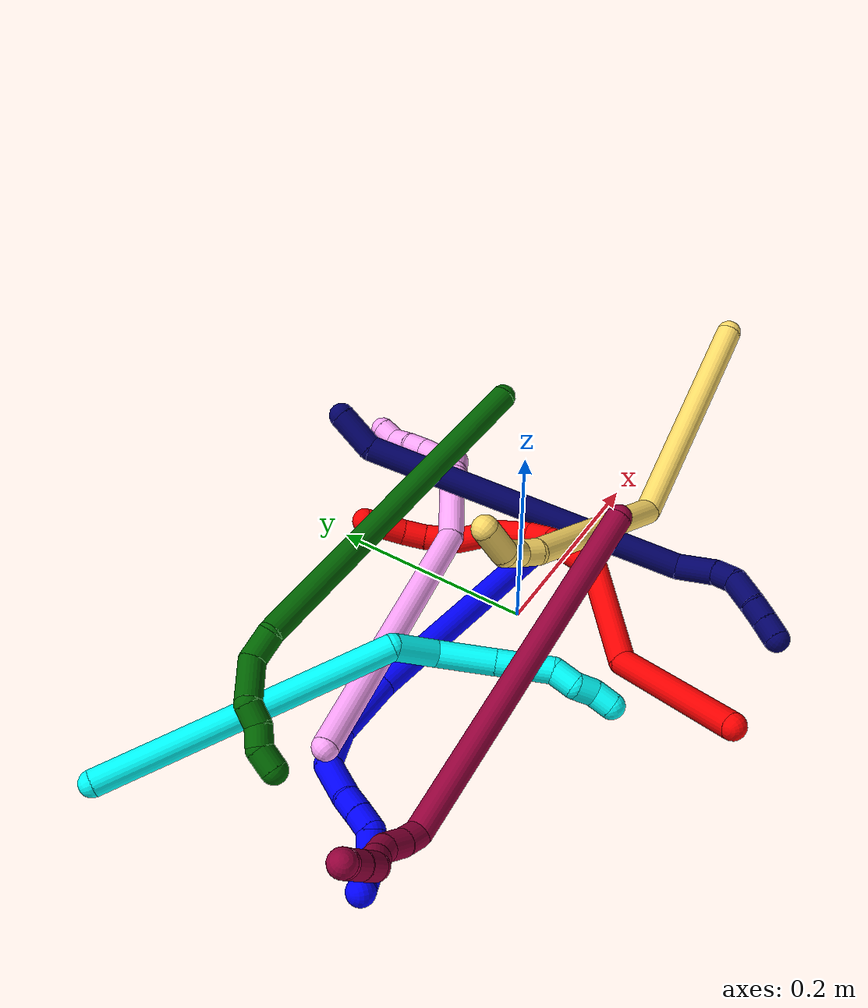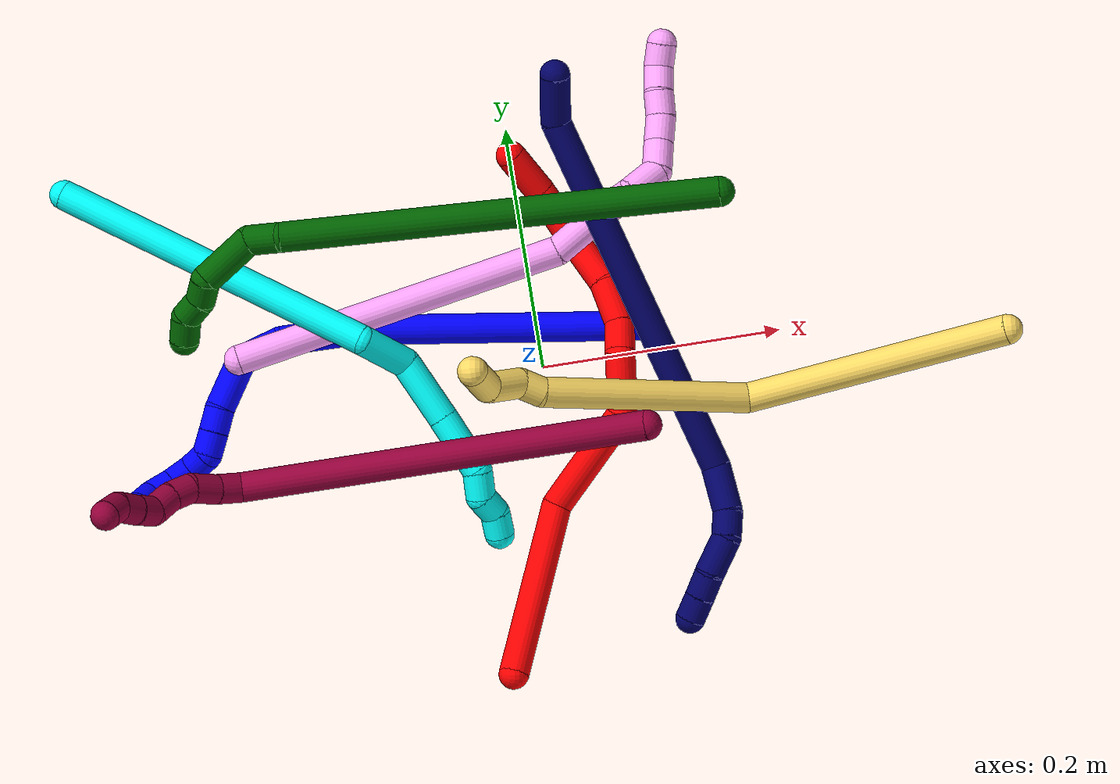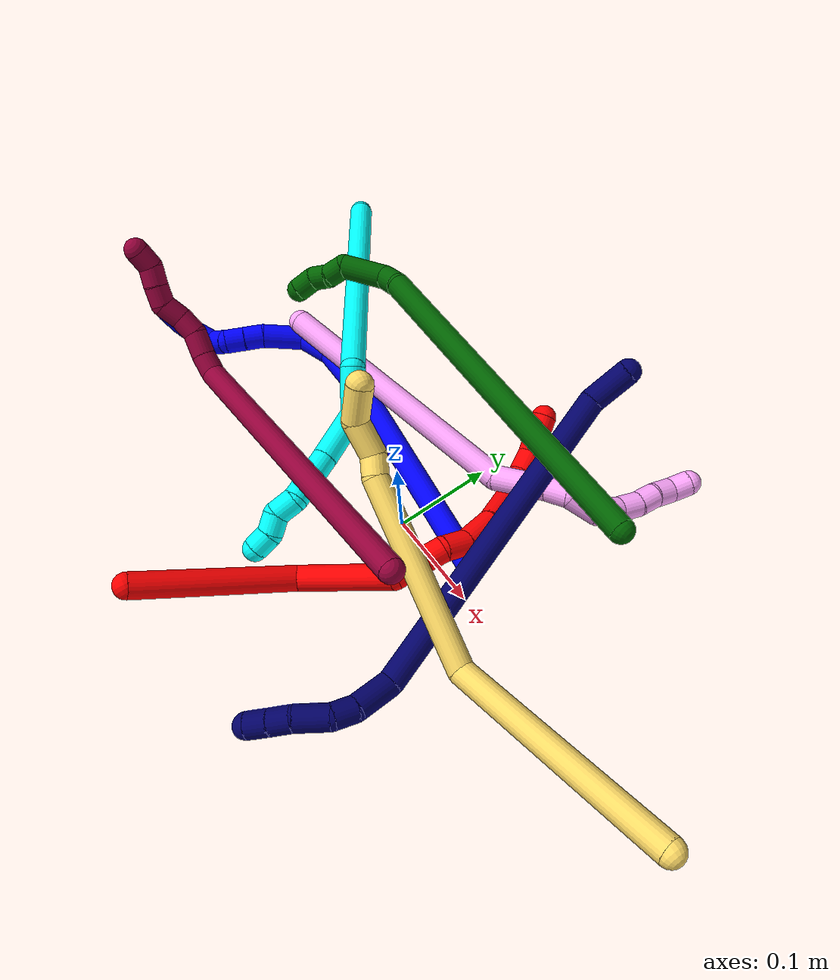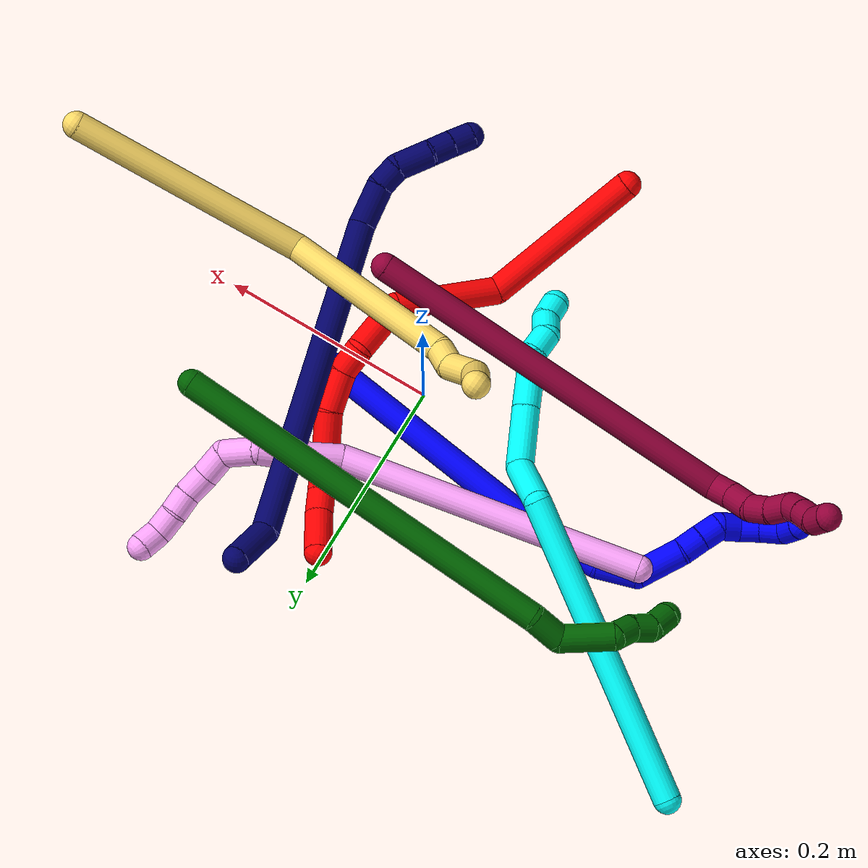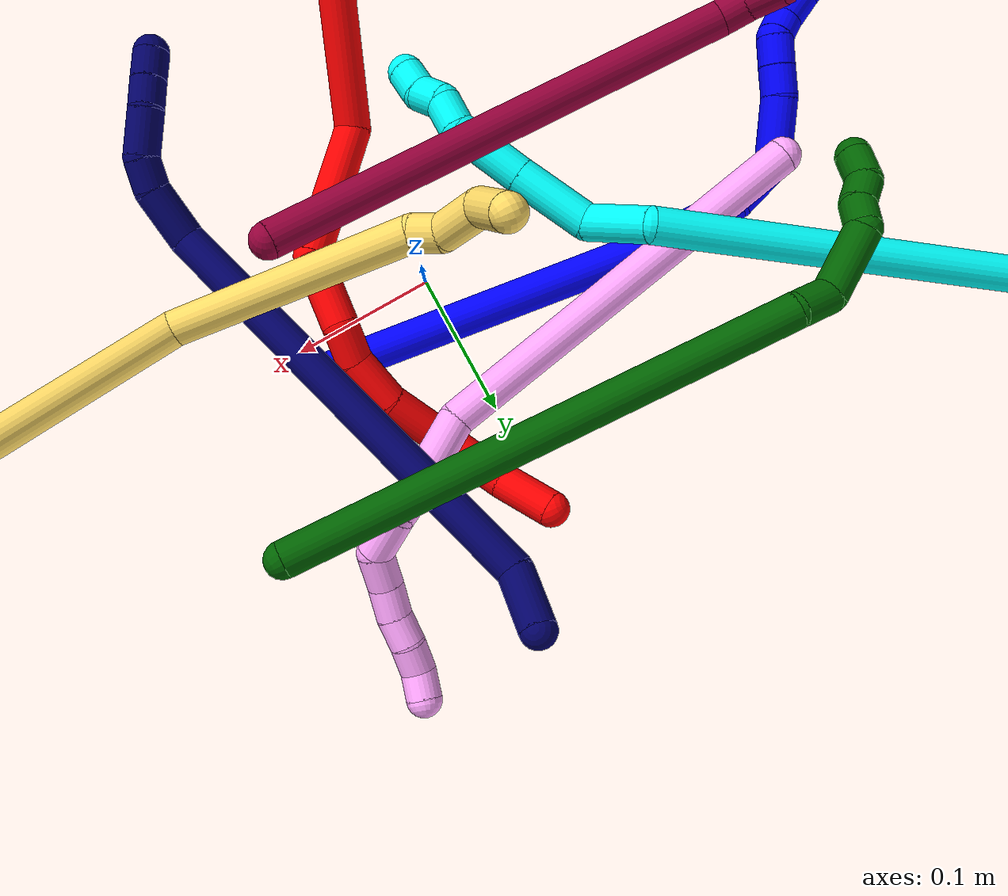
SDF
<sdf version="1.7">
 <world name="default">
  <plugin name="TubeGeneratorPlugin" filename="libtube_generator_plugin.so"/>
  <model name="photoneo_s_sensor">
   <static>1</static>
   <pose>0 0 2 1.57079 1.57079 3.14159</pose>
   <link name="link">
    <inertial><mass>0.1</mass></inertial>
    <sensor name="sensor" type="depth">
     <update_rate>30</update_rate>
     <camera>
      <horizontal_fov>1.22</horizontal_fov>
      <image><width>1920</width><height>1200</height><format>B8G8R8</format></image>
      <clip><near>0.1</near><far>4</far></clip>
      <depth_camera><output>points</output></depth_camera>
     </camera>
     <plugin name="camera_plugin" filename="libgazebo_ros_depth_camera.so">
      <baseline>0.2</baseline>
      <alwaysOn>1</alwaysOn>
      <updateRate>0.0</updateRate>
      <cameraName>camera_ir</cameraName>
      <imageTopicName>/camera/color/image_raw</imageTopicName>
      <cameraInfoTopicName>/camera/color/camera_info</cameraInfoTopicName>
      <depthImageTopicName>/camera/depth/image_raw</depthImageTopicName>
      <depthImageCameraInfoTopicName>/camera/depth/camera_info</depthImageCameraInfoTopicName>
      <pointCloudTopicName>/camera/depth/points</pointCloudTopicName>
      <frameName>fr_optical</frameName>
      <pointCloudCutoff>0.1</pointCloudCutoff>
      <pointCloudCutoffMax>2.0</pointCloudCutoffMax>
      <distortionK1>0</distortionK1>
      <distortionK2>0</distortionK2>
      <distortionK3>0</distortionK3>
      <distortionT1>0</distortionT1>
      <distortionT2>0</distortionT2>
      <CxPrime>0</CxPrime>
      <Cx>0</Cx>
      <Cy>0</Cy>
      <focalLength>0</focalLength>
      <hackBaseline>0</hackBaseline>
     </plugin>
    </sensor>
   </link>
  </model>
  <gravity>0 0 -9.8</gravity>
  <magnetic_field>6e-06 2.3e-05 -4.2e-05</magnetic_field>
  <atmosphere type="adiabatic"/>
  <physics name="default_physics" default="0" type="ode">
   <max_step_size>0.003</max_step_size>
   <real_time_factor>1</real_time_factor>
   <real_time_update_rate>1000</real_time_update_rate>
   <max_contacts>10000</max_contacts>
   <ode>
    <solver>
     <type>quick</type>
     <iters>100</iters>
     <sor>1.3</sor>
     <use_dynamic_moi_rescaling>0</use_dynamic_moi_rescaling>
    </solver>
    <constraints>
     <contact_max_correcting_vel>0</contact_max_correcting_vel>
     <contact_surface_layer>0.001</contact_surface_layer>
     <cfm>0</cfm>
     <erp>0.2</erp>
    </constraints>
   </ode>
  </physics>
  <scene><ambient>0.4 0.4 0.4 1</ambient><background>0.7 0.7 0.7 1</background><shadows>0</shadows></scene>
  <audio><device>default</device></audio>
  <spherical_coordinates>
   <surface_model>EARTH_WGS84</surface_model>
   <latitude_deg>0</latitude_deg>
   <longitude_deg>0</longitude_deg>
   <elevation>0</elevation>
   <heading_deg>0</heading_deg>
  </spherical_coordinates>
  <model name="bin">
   <static>1</static>
   <link name="bottom">
    <collision name="collision-bottom">
     <pose>0 0 -0.01 0 -0 0</pose>
     <geometry><box><size>0.8 0.6 0.02</size></box></geometry>
     <surface>
      <friction><ode><mu>100</mu><mu2>100</mu2></ode></friction>
      <contact><collide_bitmask>65535</collide_bitmask></contact>
     </surface>
    </collision>
   </link>
   <link name="west_wall">
    <collision name="collision-west_wall">
     <pose>-0.41 0 0.1 0 -0 0</pose>
     <geometry><box><size>0.02 0.6 0.2</size></box></geometry>
     <surface>
      <friction><ode><mu>100</mu><mu2>100</mu2></ode></friction>
      <contact><collide_bitmask>65535</collide_bitmask></contact>
     </surface>
    </collision>
   </link>
   <link name="east_wall">
    <collision name="collision-east_wall">
     <pose>0.41 0 0.1 0 -0 0</pose>
     <geometry><box><size>0.02 0.6 0.2</size></box></geometry>
     <surface>
      <friction><ode><mu>100</mu><mu2>100</mu2></ode></friction>
      <contact><collide_bitmask>65535</collide_bitmask></contact>
     </surface>
    </collision>
   </link>
   <link name="south_wall">
    <collision name="collision-south_wall">
     <pose>0 -0.31 0.1 0 -0 0</pose>
     <geometry><box><size>0.8 0.02 0.2</size></box></geometry>
     <surface>
      <friction><ode><mu>100</mu><mu2>100</mu2></ode></friction>
      <contact><collide_bitmask>65535</collide_bitmask></contact>
     </surface>
    </collision>
   </link>
   <link name="north_wall">
    <collision name="collision-north_wall">
     <pose>0 0.31 0.1 0 -0 0</pose>
     <geometry><box><size>0.8 0.02 0.2</size></box></geometry>
     <surface>
      <friction><ode><mu>100</mu><mu2>100</mu2></ode></friction>
      <contact><collide_bitmask>65535</collide_bitmask></contact>
     </surface>
    </collision>
   </link>
  </model>
  <model name="1">
   <static>0</static>
   <link name="1">
    <collision name="collision-cylinder-e_1_1_4">
     <pose>-0.052096 0.009545 0.104828 -0.090799 -0.459575 0.021253</pose>
     <geometry><cylinder><radius>0.0125</radius><length>0.234895</length></cylinder></geometry>
     <surface>
      <friction><ode><mu>1.16</mu><mu2>1.16</mu2><slip1>0</slip1><slip2>0</slip2></ode></friction>
      <contact><ode><kp>1e+06</kp><kd>1</kd><max_vel>0</max_vel><min_depth>0.001</min_depth></ode></contact>
     </surface>
    </collision>
    <visual name="visual-cylinder-e_1_1_4">
     <pose>-0.052096 0.009545 0.104828 -0.090799 -0.459575 0.021253</pose>
     <geometry><cylinder><radius>0.0125</radius><length>0.234895</length></cylinder></geometry>
     <material><ambient>0 0 1 1</ambient></material>
    </visual>
    <collision name="collision-cylinder-e_2_4_5">
     <pose>-0.121042 0.018943 0.236854 0.005377 -0.554649 -0.001531</pose>
     <geometry><cylinder><radius>0.0125</radius><length>0.06399</length></cylinder></geometry>
     <surface>
      <friction><ode><mu>1.16</mu><mu2>1.16</mu2><slip1>0</slip1><slip2>0</slip2></ode></friction>
      <contact><ode><kp>1e+06</kp><kd>1</kd><max_vel>0</max_vel><min_depth>0.001</min_depth></ode></contact>
     </surface>
    </collision>
    <visual name="visual-cylinder-e_2_4_5">
     <pose>-0.121042 0.018943 0.236854 0.005377 -0.554649 -0.001531</pose>
     <geometry><cylinder><radius>0.0125</radius><length>0.06399</length></cylinder></geometry>
     <material><ambient>0 0 1 1</ambient></material>
    </visual>
    <collision name="collision-cylinder-e_3_5_6">
     <pose>-0.151175 0.015774 0.276244 0.243037 -0.813323 -0.10509</pose>
     <geometry><cylinder><radius>0.0125</radius><length>0.036563</length></cylinder></geometry>
     <surface>
      <friction><ode><mu>1.16</mu><mu2>1.16</mu2><slip1>0</slip1><slip2>0</slip2></ode></friction>
      <contact><ode><kp>1e+06</kp><kd>1</kd><max_vel>0</max_vel><min_depth>0.001</min_depth></ode></contact>
     </surface>
    </collision>
    <visual name="visual-cylinder-e_3_5_6">
     <pose>-0.151175 0.015774 0.276244 0.243037 -0.813323 -0.10509</pose>
     <geometry><cylinder><radius>0.0125</radius><length>0.036563</length></cylinder></geometry>
     <material><ambient>0 0 1 1</ambient></material>
    </visual>
    <collision name="collision-cylinder-e_4_6_7">
     <pose>-0.180951 -0.001568 0.291622 1.35185 -0.843851 -0.691078</pose>
     <geometry><cylinder><radius>0.0125</radius><length>0.044145</length></cylinder></geometry>
     <surface>
      <friction><ode><mu>1.16</mu><mu2>1.16</mu2><slip1>0</slip1><slip2>0</slip2></ode></friction>
      <contact><ode><kp>1e+06</kp><kd>1</kd><max_vel>0</max_vel><min_depth>0.001</min_depth></ode></contact>
     </surface>
    </collision>
    <visual name="visual-cylinder-e_4_6_7">
     <pose>-0.180951 -0.001568 0.291622 1.35185 -0.843851 -0.691078</pose>
     <geometry><cylinder><radius>0.0125</radius><length>0.044145</length></cylinder></geometry>
     <material><ambient>0 0 1 1</ambient></material>
    </visual>
    <collision name="collision-cylinder-e_5_7_8">
     <pose>-0.205636 -0.021778 0.294328 1.65212 -0.945848 -1.01342</pose>
     <geometry><cylinder><radius>0.0125</radius><length>0.020204</length></cylinder></geometry>
     <surface>
      <friction><ode><mu>1.16</mu><mu2>1.16</mu2><slip1>0</slip1><slip2>0</slip2></ode></friction>
      <contact><ode><kp>1e+06</kp><kd>1</kd><max_vel>0</max_vel><min_depth>0.001</min_depth></ode></contact>
     </surface>
    </collision>
    <visual name="visual-cylinder-e_5_7_8">
     <pose>-0.205636 -0.021778 0.294328 1.65212 -0.945848 -1.01342</pose>
     <geometry><cylinder><radius>0.0125</radius><length>0.020204</length></cylinder></geometry>
     <material><ambient>0 0 1 1</ambient></material>
    </visual>
    <collision name="collision-cylinder-e_6_8_9">
     <pose>-0.22217 -0.033222 0.293468 1.63902 -0.982318 -1.04017</pose>
     <geometry><cylinder><radius>0.0125</radius><length>0.020056</length></cylinder></geometry>
     <surface>
      <friction><ode><mu>1.16</mu><mu2>1.16</mu2><slip1>0</slip1><slip2>0</slip2></ode></friction>
      <contact><ode><kp>1e+06</kp><kd>1</kd><max_vel>0</max_vel><min_depth>0.001</min_depth></ode></contact>
     </surface>
    </collision>
    <visual name="visual-cylinder-e_6_8_9">
     <pose>-0.22217 -0.033222 0.293468 1.63902 -0.982318 -1.04017</pose>
     <geometry><cylinder><radius>0.0125</radius><length>0.020056</length></cylinder></geometry>
     <material><ambient>0 0 1 1</ambient></material>
    </visual>
    <collision name="collision-cylinder-e_7_9_10">
     <pose>-0.240103 -0.038493 0.295917 -0.099797 -1.28267 0.074538</pose>
     <geometry><cylinder><radius>0.0125</radius><length>0.020008</length></cylinder></geometry>
     <surface>
      <friction><ode><mu>1.16</mu><mu2>1.16</mu2><slip1>0</slip1><slip2>0</slip2></ode></friction>
      <contact><ode><kp>1e+06</kp><kd>1</kd><max_vel>0</max_vel><min_depth>0.001</min_depth></ode></contact>
     </surface>
    </collision>
    <visual name="visual-cylinder-e_7_9_10">
     <pose>-0.240103 -0.038493 0.295917 -0.099797 -1.28267 0.074538</pose>
     <geometry><cylinder><radius>0.0125</radius><length>0.020008</length></cylinder></geometry>
     <material><ambient>0 0 1 1</ambient></material>
    </visual>
    <collision name="collision-cylinder-e_8_10_11">
     <pose>-0.256288 -0.042633 0.30492 0.621759 -0.714924 -0.238872</pose>
     <geometry><cylinder><radius>0.0125</radius><length>0.020116</length></cylinder></geometry>
     <surface>
      <friction><ode><mu>1.16</mu><mu2>1.16</mu2><slip1>0</slip1><slip2>0</slip2></ode></friction>
      <contact><ode><kp>1e+06</kp><kd>1</kd><max_vel>0</max_vel><min_depth>0.001</min_depth></ode></contact>
     </surface>
    </collision>
    <visual name="visual-cylinder-e_8_10_11">
     <pose>-0.256288 -0.042633 0.30492 0.621759 -0.714924 -0.238872</pose>
     <geometry><cylinder><radius>0.0125</radius><length>0.020116</length></cylinder></geometry>
     <material><ambient>0 0 1 1</ambient></material>
    </visual>
    <collision name="collision-cylinder-e_9_11_12">
     <pose>-0.268748 -0.051452 0.317912 0.572473 -0.626019 -0.189939</pose>
     <geometry><cylinder><radius>0.0125</radius><length>0.020022</length></cylinder></geometry>
     <surface>
      <friction><ode><mu>1.16</mu><mu2>1.16</mu2><slip1>0</slip1><slip2>0</slip2></ode></friction>
      <contact><ode><kp>1e+06</kp><kd>1</kd><max_vel>0</max_vel><min_depth>0.001</min_depth></ode></contact>
     </surface>
    </collision>
    <visual name="visual-cylinder-e_9_11_12">
     <pose>-0.268748 -0.051452 0.317912 0.572473 -0.626019 -0.189939</pose>
     <geometry><cylinder><radius>0.0125</radius><length>0.020022</length></cylinder></geometry>
     <material><ambient>0 0 1 1</ambient></material>
    </visual>
    <collision name="collision-cylinder-e_10_12_2">
     <pose>-0.275382 -0.064253 0.330093 1.00309 -0.076933 -0.042198</pose>
     <geometry><cylinder><radius>0.0125</radius><length>0.02</length></cylinder></geometry>
     <surface>
      <friction><ode><mu>1.16</mu><mu2>1.16</mu2><slip1>0</slip1><slip2>0</slip2></ode></friction>
      <contact><ode><kp>1e+06</kp><kd>1</kd><max_vel>0</max_vel><min_depth>0.001</min_depth></ode></contact>
     </surface>
    </collision>
    <visual name="visual-cylinder-e_10_12_2">
     <pose>-0.275382 -0.064253 0.330093 1.00309 -0.076933 -0.042198</pose>
     <geometry><cylinder><radius>0.0125</radius><length>0.02</length></cylinder></geometry>
     <material><ambient>0 0 1 1</ambient></material>
    </visual>
    <collision name="collision-sphere-2">
     <pose>-0.27615 -0.072659 0.335454 0 -0 0</pose>
     <geometry><sphere><radius>0.0125</radius></sphere></geometry>
     <surface>
      <friction><ode><mu>1.16</mu><mu2>1.16</mu2><slip1>0</slip1><slip2>0</slip2></ode></friction>
      <contact><ode><kp>1e+06</kp><kd>1</kd><max_vel>0</max_vel><min_depth>0.001</min_depth></ode></contact>
     </surface>
    </collision>
    <visual name="visual-sphere-2">
     <pose>-0.27615 -0.072659 0.335454 0 -0 0</pose>
     <geometry><sphere><radius>0.0125</radius></sphere></geometry>
     <material><ambient>0 0 1 1</ambient></material>
    </visual>
    <collision name="collision-sphere-12">
     <pose>-0.274613 -0.055847 0.324732 0 -0 0</pose>
     <geometry><sphere><radius>0.0125</radius></sphere></geometry>
     <surface>
      <friction><ode><mu>1.16</mu><mu2>1.16</mu2><slip1>0</slip1><slip2>0</slip2></ode></friction>
      <contact><ode><kp>1e+06</kp><kd>1</kd><max_vel>0</max_vel><min_depth>0.001</min_depth></ode></contact>
     </surface>
    </collision>
    <visual name="visual-sphere-12">
     <pose>-0.274613 -0.055847 0.324732 0 -0 0</pose>
     <geometry><sphere><radius>0.0125</radius></sphere></geometry>
     <material><ambient>0 0 1 1</ambient></material>
    </visual>
    <collision name="collision-sphere-11">
     <pose>-0.262882 -0.047057 0.311093 0 -0 0</pose>
     <geometry><sphere><radius>0.0125</radius></sphere></geometry>
     <surface>
      <friction><ode><mu>1.16</mu><mu2>1.16</mu2><slip1>0</slip1><slip2>0</slip2></ode></friction>
      <contact><ode><kp>1e+06</kp><kd>1</kd><max_vel>0</max_vel><min_depth>0.001</min_depth></ode></contact>
     </surface>
    </collision>
    <visual name="visual-sphere-11">
     <pose>-0.262882 -0.047057 0.311093 0 -0 0</pose>
     <geometry><sphere><radius>0.0125</radius></sphere></geometry>
     <material><ambient>0 0 1 1</ambient></material>
    </visual>
    <collision name="collision-sphere-10">
     <pose>-0.249695 -0.03821 0.298746 0 -0 0</pose>
     <geometry><sphere><radius>0.0125</radius></sphere></geometry>
     <surface>
      <friction><ode><mu>1.16</mu><mu2>1.16</mu2><slip1>0</slip1><slip2>0</slip2></ode></friction>
      <contact><ode><kp>1e+06</kp><kd>1</kd><max_vel>0</max_vel><min_depth>0.001</min_depth></ode></contact>
     </surface>
    </collision>
    <visual name="visual-sphere-10">
     <pose>-0.249695 -0.03821 0.298746 0 -0 0</pose>
     <geometry><sphere><radius>0.0125</radius></sphere></geometry>
     <material><ambient>0 0 1 1</ambient></material>
    </visual>
    <collision name="collision-sphere-9">
     <pose>-0.230511 -0.038776 0.293089 0 -0 0</pose>
     <geometry><sphere><radius>0.0125</radius></sphere></geometry>
     <surface>
      <friction><ode><mu>1.16</mu><mu2>1.16</mu2><slip1>0</slip1><slip2>0</slip2></ode></friction>
      <contact><ode><kp>1e+06</kp><kd>1</kd><max_vel>0</max_vel><min_depth>0.001</min_depth></ode></contact>
     </surface>
    </collision>
    <visual name="visual-sphere-9">
     <pose>-0.230511 -0.038776 0.293089 0 -0 0</pose>
     <geometry><sphere><radius>0.0125</radius></sphere></geometry>
     <material><ambient>0 0 1 1</ambient></material>
    </visual>
    <collision name="collision-sphere-4">
     <pose>-0.104192 0.019089 0.209656 0 -0 0</pose>
     <geometry><sphere><radius>0.0125</radius></sphere></geometry>
     <surface>
      <friction><ode><mu>1.16</mu><mu2>1.16</mu2><slip1>0</slip1><slip2>0</slip2></ode></friction>
      <contact><ode><kp>1e+06</kp><kd>1</kd><max_vel>0</max_vel><min_depth>0.001</min_depth></ode></contact>
     </surface>
    </collision>
    <visual name="visual-sphere-4">
     <pose>-0.104192 0.019089 0.209656 0 -0 0</pose>
     <geometry><sphere><radius>0.0125</radius></sphere></geometry>
     <material><ambient>0 0 1 1</ambient></material>
    </visual>
    <collision name="collision-sphere-1">
     <geometry><sphere><radius>0.0125</radius></sphere></geometry>
     <surface>
      <friction><ode><mu>1.16</mu><mu2>1.16</mu2><slip1>0</slip1><slip2>0</slip2></ode></friction>
      <contact><ode><kp>1e+06</kp><kd>1</kd><max_vel>0</max_vel><min_depth>0.001</min_depth></ode></contact>
     </surface>
    </collision>
    <visual name="visual-sphere-1">
     <geometry><sphere><radius>0.0125</radius></sphere></geometry>
     <material><ambient>0 0 1 1</ambient></material>
    </visual>
    <collision name="collision-sphere-8">
     <pose>-0.213829 -0.027669 0.293848 0 -0 0</pose>
     <geometry><sphere><radius>0.0125</radius></sphere></geometry>
     <surface>
      <friction><ode><mu>1.16</mu><mu2>1.16</mu2><slip1>0</slip1><slip2>0</slip2></ode></friction>
      <contact><ode><kp>1e+06</kp><kd>1</kd><max_vel>0</max_vel><min_depth>0.001</min_depth></ode></contact>
     </surface>
    </collision>
    <visual name="visual-sphere-8">
     <pose>-0.213829 -0.027669 0.293848 0 -0 0</pose>
     <geometry><sphere><radius>0.0125</radius></sphere></geometry>
     <material><ambient>0 0 1 1</ambient></material>
    </visual>
    <collision name="collision-sphere-5">
     <pose>-0.137892 0.018797 0.264052 0 -0 0</pose>
     <geometry><sphere><radius>0.0125</radius></sphere></geometry>
     <surface>
      <friction><ode><mu>1.16</mu><mu2>1.16</mu2><slip1>0</slip1><slip2>0</slip2></ode></friction>
      <contact><ode><kp>1e+06</kp><kd>1</kd><max_vel>0</max_vel><min_depth>0.001</min_depth></ode></contact>
     </surface>
    </collision>
    <visual name="visual-sphere-5">
     <pose>-0.137892 0.018797 0.264052 0 -0 0</pose>
     <geometry><sphere><radius>0.0125</radius></sphere></geometry>
     <material><ambient>0 0 1 1</ambient></material>
    </visual>
    <collision name="collision-sphere-6">
     <pose>-0.164458 0.012751 0.288436 0 -0 0</pose>
     <geometry><sphere><radius>0.0125</radius></sphere></geometry>
     <surface>
      <friction><ode><mu>1.16</mu><mu2>1.16</mu2><slip1>0</slip1><slip2>0</slip2></ode></friction>
      <contact><ode><kp>1e+06</kp><kd>1</kd><max_vel>0</max_vel><min_depth>0.001</min_depth></ode></contact>
     </surface>
    </collision>
    <visual name="visual-sphere-6">
     <pose>-0.164458 0.012751 0.288436 0 -0 0</pose>
     <geometry><sphere><radius>0.0125</radius></sphere></geometry>
     <material><ambient>0 0 1 1</ambient></material>
    </visual>
    <collision name="collision-sphere-7">
     <pose>-0.197444 -0.015887 0.294808 0 -0 0</pose>
     <geometry><sphere><radius>0.0125</radius></sphere></geometry>
     <surface>
      <friction><ode><mu>1.16</mu><mu2>1.16</mu2><slip1>0</slip1><slip2>0</slip2></ode></friction>
      <contact><ode><kp>1e+06</kp><kd>1</kd><max_vel>0</max_vel><min_depth>0.001</min_depth></ode></contact>
     </surface>
    </collision>
    <visual name="visual-sphere-7">
     <pose>-0.197444 -0.015887 0.294808 0 -0 0</pose>
     <geometry><sphere><radius>0.0125</radius></sphere></geometry>
     <material><ambient>0 0 1 1</ambient></material>
    </visual>
    <inertial>
     <pose>-0.125913 -0.002175 0.199216 0 -0 0</pose>
     <mass>0.5</mass>
     <inertia>
      <ixx>0.001003</ixx>
      <ixy>0</ixy>
      <ixz>0</ixz>
      <iyy>0.001136</iyy>
      <iyz>0</iyz>
      <izz>0.000461</izz>
     </inertia>
    </inertial>
   </link>
   <pose>0.084291 0.021603 0.011498 -1.17536 -0.538617 0.883763</pose>
  </model>
  <model name="2">
   <static>0</static>
   <link name="2">
    <collision name="collision-cylinder-e_1_1_4">
     <pose>0.003201 0.069492 -0.030069 -1.97916 0.04225 -0.064304</pose>
     <geometry><cylinder><radius>0.0125</radius><length>0.151572</length></cylinder></geometry>
     <surface>
      <friction><ode><mu>1.16</mu><mu2>1.16</mu2><slip1>0</slip1><slip2>0</slip2></ode></friction>
      <contact><ode><kp>1e+06</kp><kd>1</kd><max_vel>0</max_vel><min_depth>0.001</min_depth></ode></contact>
     </surface>
    </collision>
    <visual name="visual-cylinder-e_1_1_4">
     <pose>0.003201 0.069492 -0.030069 -1.97916 0.04225 -0.064304</pose>
     <geometry><cylinder><radius>0.0125</radius><length>0.151572</length></cylinder></geometry>
     <material><ambient>1 0 0 1</ambient></material>
    </visual>
    <collision name="collision-cylinder-e_2_4_5">
     <pose>0.0408 0.166781 -0.081696 -2.23047 0.774196 -1.388</pose>
     <geometry><cylinder><radius>0.0125</radius><length>0.0984</length></cylinder></geometry>
     <surface>
      <friction><ode><mu>1.16</mu><mu2>1.16</mu2><slip1>0</slip1><slip2>0</slip2></ode></friction>
      <contact><ode><kp>1e+06</kp><kd>1</kd><max_vel>0</max_vel><min_depth>0.001</min_depth></ode></contact>
     </surface>
    </collision>
    <visual name="visual-cylinder-e_2_4_5">
     <pose>0.0408 0.166781 -0.081696 -2.23047 0.774196 -1.388</pose>
     <geometry><cylinder><radius>0.0125</radius><length>0.0984</length></cylinder></geometry>
     <material><ambient>1 0 0 1</ambient></material>
    </visual>
    <collision name="collision-cylinder-e_3_5_6">
     <pose>0.084958 0.218039 -0.10255 -1.54075 0.39407 -0.382692</pose>
     <geometry><cylinder><radius>0.0125</radius><length>0.050839</length></cylinder></geometry>
     <surface>
      <friction><ode><mu>1.16</mu><mu2>1.16</mu2><slip1>0</slip1><slip2>0</slip2></ode></friction>
      <contact><ode><kp>1e+06</kp><kd>1</kd><max_vel>0</max_vel><min_depth>0.001</min_depth></ode></contact>
     </surface>
    </collision>
    <visual name="visual-cylinder-e_3_5_6">
     <pose>0.084958 0.218039 -0.10255 -1.54075 0.39407 -0.382692</pose>
     <geometry><cylinder><radius>0.0125</radius><length>0.050839</length></cylinder></geometry>
     <material><ambient>1 0 0 1</ambient></material>
    </visual>
    <collision name="collision-cylinder-e_4_6_7">
     <pose>0.09453 0.254264 -0.10402 -1.73961 -0.014492 0.017171</pose>
     <geometry><cylinder><radius>0.0125</radius><length>0.025901</length></cylinder></geometry>
     <surface>
      <friction><ode><mu>1.16</mu><mu2>1.16</mu2><slip1>0</slip1><slip2>0</slip2></ode></friction>
      <contact><ode><kp>1e+06</kp><kd>1</kd><max_vel>0</max_vel><min_depth>0.001</min_depth></ode></contact>
     </surface>
    </collision>
    <visual name="visual-cylinder-e_4_6_7">
     <pose>0.09453 0.254264 -0.10402 -1.73961 -0.014492 0.017171</pose>
     <geometry><cylinder><radius>0.0125</radius><length>0.025901</length></cylinder></geometry>
     <material><ambient>1 0 0 1</ambient></material>
    </visual>
    <collision name="collision-cylinder-e_5_7_8">
     <pose>0.093548 0.28514 -0.102915 -1.39159 -0.043101 0.035996</pose>
     <geometry><cylinder><radius>0.0125</radius><length>0.036845</length></cylinder></geometry>
     <surface>
      <friction><ode><mu>1.16</mu><mu2>1.16</mu2><slip1>0</slip1><slip2>0</slip2></ode></friction>
      <contact><ode><kp>1e+06</kp><kd>1</kd><max_vel>0</max_vel><min_depth>0.001</min_depth></ode></contact>
     </surface>
    </collision>
    <visual name="visual-cylinder-e_5_7_8">
     <pose>0.093548 0.28514 -0.102915 -1.39159 -0.043101 0.035996</pose>
     <geometry><cylinder><radius>0.0125</radius><length>0.036845</length></cylinder></geometry>
     <material><ambient>1 0 0 1</ambient></material>
    </visual>
    <collision name="collision-cylinder-e_6_8_9">
     <pose>0.087153 0.322217 -0.092946 -1.23179 -0.271647 0.192844</pose>
     <geometry><cylinder><radius>0.0125</radius><length>0.041753</length></cylinder></geometry>
     <surface>
      <friction><ode><mu>1.16</mu><mu2>1.16</mu2><slip1>0</slip1><slip2>0</slip2></ode></friction>
      <contact><ode><kp>1e+06</kp><kd>1</kd><max_vel>0</max_vel><min_depth>0.001</min_depth></ode></contact>
     </surface>
    </collision>
    <visual name="visual-cylinder-e_6_8_9">
     <pose>0.087153 0.322217 -0.092946 -1.23179 -0.271647 0.192844</pose>
     <geometry><cylinder><radius>0.0125</radius><length>0.041753</length></cylinder></geometry>
     <material><ambient>1 0 0 1</ambient></material>
    </visual>
    <collision name="collision-cylinder-e_7_9_10">
     <pose>0.083096 0.355043 -0.078282 -1.04857 0.09633 -0.055733</pose>
     <geometry><cylinder><radius>0.0125</radius><length>0.032131</length></cylinder></geometry>
     <surface>
      <friction><ode><mu>1.16</mu><mu2>1.16</mu2><slip1>0</slip1><slip2>0</slip2></ode></friction>
      <contact><ode><kp>1e+06</kp><kd>1</kd><max_vel>0</max_vel><min_depth>0.001</min_depth></ode></contact>
     </surface>
    </collision>
    <visual name="visual-cylinder-e_7_9_10">
     <pose>0.083096 0.355043 -0.078282 -1.04857 0.09633 -0.055733</pose>
     <geometry><cylinder><radius>0.0125</radius><length>0.032131</length></cylinder></geometry>
     <material><ambient>1 0 0 1</ambient></material>
    </visual>
    <collision name="collision-cylinder-e_8_10_11">
     <pose>0.087536 0.377778 -0.063917 -0.946888 0.258732 -0.133097</pose>
     <geometry><cylinder><radius>0.0125</radius><length>0.022624</length></cylinder></geometry>
     <surface>
      <friction><ode><mu>1.16</mu><mu2>1.16</mu2><slip1>0</slip1><slip2>0</slip2></ode></friction>
      <contact><ode><kp>1e+06</kp><kd>1</kd><max_vel>0</max_vel><min_depth>0.001</min_depth></ode></contact>
     </surface>
    </collision>
    <visual name="visual-cylinder-e_8_10_11">
     <pose>0.087536 0.377778 -0.063917 -0.946888 0.258732 -0.133097</pose>
     <geometry><cylinder><radius>0.0125</radius><length>0.022624</length></cylinder></geometry>
     <material><ambient>1 0 0 1</ambient></material>
    </visual>
    <collision name="collision-cylinder-e_9_11_2">
     <pose>0.097368 0.399978 -0.044375 -0.791863 0.354894 -0.149645</pose>
     <geometry><cylinder><radius>0.0125</radius><length>0.039934</length></cylinder></geometry>
     <surface>
      <friction><ode><mu>1.16</mu><mu2>1.16</mu2><slip1>0</slip1><slip2>0</slip2></ode></friction>
      <contact><ode><kp>1e+06</kp><kd>1</kd><max_vel>0</max_vel><min_depth>0.001</min_depth></ode></contact>
     </surface>
    </collision>
    <visual name="visual-cylinder-e_9_11_2">
     <pose>0.097368 0.399978 -0.044375 -0.791863 0.354894 -0.149645</pose>
     <geometry><cylinder><radius>0.0125</radius><length>0.039934</length></cylinder></geometry>
     <material><ambient>1 0 0 1</ambient></material>
    </visual>
    <collision name="collision-sphere-2">
     <pose>0.104307 0.413302 -0.031222 0 -0 0</pose>
     <geometry><sphere><radius>0.0125</radius></sphere></geometry>
     <surface>
      <friction><ode><mu>1.16</mu><mu2>1.16</mu2><slip1>0</slip1><slip2>0</slip2></ode></friction>
      <contact><ode><kp>1e+06</kp><kd>1</kd><max_vel>0</max_vel><min_depth>0.001</min_depth></ode></contact>
     </surface>
    </collision>
    <visual name="visual-sphere-2">
     <pose>0.104307 0.413302 -0.031222 0 -0 0</pose>
     <geometry><sphere><radius>0.0125</radius></sphere></geometry>
     <material><ambient>1 0 0 1</ambient></material>
    </visual>
    <collision name="collision-sphere-11">
     <pose>0.09043 0.386653 -0.057528 0 -0 0</pose>
     <geometry><sphere><radius>0.0125</radius></sphere></geometry>
     <surface>
      <friction><ode><mu>1.16</mu><mu2>1.16</mu2><slip1>0</slip1><slip2>0</slip2></ode></friction>
      <contact><ode><kp>1e+06</kp><kd>1</kd><max_vel>0</max_vel><min_depth>0.001</min_depth></ode></contact>
     </surface>
    </collision>
    <visual name="visual-sphere-11">
     <pose>0.09043 0.386653 -0.057528 0 -0 0</pose>
     <geometry><sphere><radius>0.0125</radius></sphere></geometry>
     <material><ambient>1 0 0 1</ambient></material>
    </visual>
    <collision name="collision-sphere-10">
     <pose>0.084642 0.368903 -0.070305 0 -0 0</pose>
     <geometry><sphere><radius>0.0125</radius></sphere></geometry>
     <surface>
      <friction><ode><mu>1.16</mu><mu2>1.16</mu2><slip1>0</slip1><slip2>0</slip2></ode></friction>
      <contact><ode><kp>1e+06</kp><kd>1</kd><max_vel>0</max_vel><min_depth>0.001</min_depth></ode></contact>
     </surface>
    </collision>
    <visual name="visual-sphere-10">
     <pose>0.084642 0.368903 -0.070305 0 -0 0</pose>
     <geometry><sphere><radius>0.0125</radius></sphere></geometry>
     <material><ambient>1 0 0 1</ambient></material>
    </visual>
    <collision name="collision-sphere-9">
     <pose>0.081551 0.341184 -0.086258 0 -0 0</pose>
     <geometry><sphere><radius>0.0125</radius></sphere></geometry>
     <surface>
      <friction><ode><mu>1.16</mu><mu2>1.16</mu2><slip1>0</slip1><slip2>0</slip2></ode></friction>
      <contact><ode><kp>1e+06</kp><kd>1</kd><max_vel>0</max_vel><min_depth>0.001</min_depth></ode></contact>
     </surface>
    </collision>
    <visual name="visual-sphere-9">
     <pose>0.081551 0.341184 -0.086258 0 -0 0</pose>
     <geometry><sphere><radius>0.0125</radius></sphere></geometry>
     <material><ambient>1 0 0 1</ambient></material>
    </visual>
    <collision name="collision-sphere-4">
     <pose>0.006402 0.138984 -0.060137 0 -0 0</pose>
     <geometry><sphere><radius>0.0125</radius></sphere></geometry>
     <surface>
      <friction><ode><mu>1.16</mu><mu2>1.16</mu2><slip1>0</slip1><slip2>0</slip2></ode></friction>
      <contact><ode><kp>1e+06</kp><kd>1</kd><max_vel>0</max_vel><min_depth>0.001</min_depth></ode></contact>
     </surface>
    </collision>
    <visual name="visual-sphere-4">
     <pose>0.006402 0.138984 -0.060137 0 -0 0</pose>
     <geometry><sphere><radius>0.0125</radius></sphere></geometry>
     <material><ambient>1 0 0 1</ambient></material>
    </visual>
    <collision name="collision-sphere-1">
     <geometry><sphere><radius>0.0125</radius></sphere></geometry>
     <surface>
      <friction><ode><mu>1.16</mu><mu2>1.16</mu2><slip1>0</slip1><slip2>0</slip2></ode></friction>
      <contact><ode><kp>1e+06</kp><kd>1</kd><max_vel>0</max_vel><min_depth>0.001</min_depth></ode></contact>
     </surface>
    </collision>
    <visual name="visual-sphere-1">
     <geometry><sphere><radius>0.0125</radius></sphere></geometry>
     <material><ambient>1 0 0 1</ambient></material>
    </visual>
    <collision name="collision-sphere-8">
     <pose>0.092754 0.30325 -0.099634 0 -0 0</pose>
     <geometry><sphere><radius>0.0125</radius></sphere></geometry>
     <surface>
      <friction><ode><mu>1.16</mu><mu2>1.16</mu2><slip1>0</slip1><slip2>0</slip2></ode></friction>
      <contact><ode><kp>1e+06</kp><kd>1</kd><max_vel>0</max_vel><min_depth>0.001</min_depth></ode></contact>
     </surface>
    </collision>
    <visual name="visual-sphere-8">
     <pose>0.092754 0.30325 -0.099634 0 -0 0</pose>
     <geometry><sphere><radius>0.0125</radius></sphere></geometry>
     <material><ambient>1 0 0 1</ambient></material>
    </visual>
    <collision name="collision-sphere-5">
     <pose>0.075198 0.194578 -0.103255 0 -0 0</pose>
     <geometry><sphere><radius>0.0125</radius></sphere></geometry>
     <surface>
      <friction><ode><mu>1.16</mu><mu2>1.16</mu2><slip1>0</slip1><slip2>0</slip2></ode></friction>
      <contact><ode><kp>1e+06</kp><kd>1</kd><max_vel>0</max_vel><min_depth>0.001</min_depth></ode></contact>
     </surface>
    </collision>
    <visual name="visual-sphere-5">
     <pose>0.075198 0.194578 -0.103255 0 -0 0</pose>
     <geometry><sphere><radius>0.0125</radius></sphere></geometry>
     <material><ambient>1 0 0 1</ambient></material>
    </visual>
    <collision name="collision-sphere-6">
     <pose>0.094717 0.241499 -0.101845 0 -0 0</pose>
     <geometry><sphere><radius>0.0125</radius></sphere></geometry>
     <surface>
      <friction><ode><mu>1.16</mu><mu2>1.16</mu2><slip1>0</slip1><slip2>0</slip2></ode></friction>
      <contact><ode><kp>1e+06</kp><kd>1</kd><max_vel>0</max_vel><min_depth>0.001</min_depth></ode></contact>
     </surface>
    </collision>
    <visual name="visual-sphere-6">
     <pose>0.094717 0.241499 -0.101845 0 -0 0</pose>
     <geometry><sphere><radius>0.0125</radius></sphere></geometry>
     <material><ambient>1 0 0 1</ambient></material>
    </visual>
    <collision name="collision-sphere-7">
     <pose>0.094342 0.267029 -0.106196 0 -0 0</pose>
     <geometry><sphere><radius>0.0125</radius></sphere></geometry>
     <surface>
      <friction><ode><mu>1.16</mu><mu2>1.16</mu2><slip1>0</slip1><slip2>0</slip2></ode></friction>
      <contact><ode><kp>1e+06</kp><kd>1</kd><max_vel>0</max_vel><min_depth>0.001</min_depth></ode></contact>
     </surface>
    </collision>
    <visual name="visual-sphere-7">
     <pose>0.094342 0.267029 -0.106196 0 -0 0</pose>
     <geometry><sphere><radius>0.0125</radius></sphere></geometry>
     <material><ambient>1 0 0 1</ambient></material>
    </visual>
    <inertial>
     <pose>0.053784 0.209004 -0.067821 0 -0 0</pose>
     <mass>0.5</mass>
     <inertia>
      <ixx>0.000271</ixx>
      <ixy>0</ixy>
      <ixz>0</ixz>
      <iyy>-0.000116</iyy>
      <iyz>0</iyz>
      <izz>-0.000434</izz>
     </inertia>
    </inertial>
   </link>
   <pose>-0.063325 -0.244188 0.067193 -0.648793 -1.0869 0.602614</pose>
  </model>
  <model name="3">
   <static>0</static>
   <link name="3">
    <collision name="collision-cylinder-e_1_1_4">
     <pose>0.00477 -0.004207 -0.141288 3.11183 0.033732 1.69556</pose>
     <geometry><cylinder><radius>0.0125</radius><length>0.282862</length></cylinder></geometry>
     <surface>
      <friction><ode><mu>1.16</mu><mu2>1.16</mu2><slip1>0</slip1><slip2>0</slip2></ode></friction>
      <contact><ode><kp>1e+06</kp><kd>1</kd><max_vel>0</max_vel><min_depth>0.001</min_depth></ode></contact>
     </surface>
    </collision>
    <visual name="visual-cylinder-e_1_1_4">
     <pose>0.00477 -0.004207 -0.141288 3.11183 0.033732 1.69556</pose>
     <geometry><cylinder><radius>0.0125</radius><length>0.282862</length></cylinder></geometry>
     <material><ambient>0.003922 1 0.996078 1</ambient></material>
    </visual>
    <collision name="collision-cylinder-e_2_4_5">
     <pose>-0.001239 -0.020375 -0.299661 2.53081 -0.477003 -1.31388</pose>
     <geometry><cylinder><radius>0.0125</radius><length>0.046952</length></cylinder></geometry>
     <surface>
      <friction><ode><mu>1.16</mu><mu2>1.16</mu2><slip1>0</slip1><slip2>0</slip2></ode></friction>
      <contact><ode><kp>1e+06</kp><kd>1</kd><max_vel>0</max_vel><min_depth>0.001</min_depth></ode></contact>
     </surface>
    </collision>
    <visual name="visual-cylinder-e_2_4_5">
     <pose>-0.001239 -0.020375 -0.299661 2.53081 -0.477003 -1.31388</pose>
     <geometry><cylinder><radius>0.0125</radius><length>0.046952</length></cylinder></geometry>
     <material><ambient>0.003922 1 0.996078 1</ambient></material>
    </visual>
    <collision name="collision-cylinder-e_3_5_6">
     <pose>-0.006947 -0.047542 -0.338999 2.54212 0.185948 0.586053</pose>
     <geometry><cylinder><radius>0.0125</radius><length>0.05485</length></cylinder></geometry>
     <surface>
      <friction><ode><mu>1.16</mu><mu2>1.16</mu2><slip1>0</slip1><slip2>0</slip2></ode></friction>
      <contact><ode><kp>1e+06</kp><kd>1</kd><max_vel>0</max_vel><min_depth>0.001</min_depth></ode></contact>
     </surface>
    </collision>
    <visual name="visual-cylinder-e_3_5_6">
     <pose>-0.006947 -0.047542 -0.338999 2.54212 0.185948 0.586053</pose>
     <geometry><cylinder><radius>0.0125</radius><length>0.05485</length></cylinder></geometry>
     <material><ambient>0.003922 1 0.996078 1</ambient></material>
    </visual>
    <collision name="collision-cylinder-e_4_6_7">
     <pose>0.003996 -0.076927 -0.382306 2.54894 0.227357 0.715682</pose>
     <geometry><cylinder><radius>0.0125</radius><length>0.052108</length></cylinder></geometry>
     <surface>
      <friction><ode><mu>1.16</mu><mu2>1.16</mu2><slip1>0</slip1><slip2>0</slip2></ode></friction>
      <contact><ode><kp>1e+06</kp><kd>1</kd><max_vel>0</max_vel><min_depth>0.001</min_depth></ode></contact>
     </surface>
    </collision>
    <visual name="visual-cylinder-e_4_6_7">
     <pose>0.003996 -0.076927 -0.382306 2.54894 0.227357 0.715682</pose>
     <geometry><cylinder><radius>0.0125</radius><length>0.052108</length></cylinder></geometry>
     <material><ambient>0.003922 1 0.996078 1</ambient></material>
    </visual>
    <collision name="collision-cylinder-e_5_7_8">
     <pose>0.013233 -0.100929 -0.40828 2.0351 0.297129 0.475519</pose>
     <geometry><cylinder><radius>0.0125</radius><length>0.02298</length></cylinder></geometry>
     <surface>
      <friction><ode><mu>1.16</mu><mu2>1.16</mu2><slip1>0</slip1><slip2>0</slip2></ode></friction>
      <contact><ode><kp>1e+06</kp><kd>1</kd><max_vel>0</max_vel><min_depth>0.001</min_depth></ode></contact>
     </surface>
    </collision>
    <visual name="visual-cylinder-e_5_7_8">
     <pose>0.013233 -0.100929 -0.40828 2.0351 0.297129 0.475519</pose>
     <geometry><cylinder><radius>0.0125</radius><length>0.02298</length></cylinder></geometry>
     <material><ambient>0.003922 1 0.996078 1</ambient></material>
    </visual>
    <collision name="collision-cylinder-e_6_8_9">
     <pose>0.014395 -0.117766 -0.420088 2.34716 -0.220321 -0.51558</pose>
     <geometry><cylinder><radius>0.0125</radius><length>0.020148</length></cylinder></geometry>
     <surface>
      <friction><ode><mu>1.16</mu><mu2>1.16</mu2><slip1>0</slip1><slip2>0</slip2></ode></friction>
      <contact><ode><kp>1e+06</kp><kd>1</kd><max_vel>0</max_vel><min_depth>0.001</min_depth></ode></contact>
     </surface>
    </collision>
    <visual name="visual-cylinder-e_6_8_9">
     <pose>0.014395 -0.117766 -0.420088 2.34716 -0.220321 -0.51558</pose>
     <geometry><cylinder><radius>0.0125</radius><length>0.020148</length></cylinder></geometry>
     <material><ambient>0.003922 1 0.996078 1</ambient></material>
    </visual>
    <collision name="collision-cylinder-e_7_9_2">
     <pose>0.013644 -0.133647 -0.431477 2.04051 0.144822 0.235246</pose>
     <geometry><cylinder><radius>0.0125</radius><length>0.0201</length></cylinder></geometry>
     <surface>
      <friction><ode><mu>1.16</mu><mu2>1.16</mu2><slip1>0</slip1><slip2>0</slip2></ode></friction>
      <contact><ode><kp>1e+06</kp><kd>1</kd><max_vel>0</max_vel><min_depth>0.001</min_depth></ode></contact>
     </surface>
    </collision>
    <visual name="visual-cylinder-e_7_9_2">
     <pose>0.013644 -0.133647 -0.431477 2.04051 0.144822 0.235246</pose>
     <geometry><cylinder><radius>0.0125</radius><length>0.0201</length></cylinder></geometry>
     <material><ambient>0.003922 1 0.996078 1</ambient></material>
    </visual>
    <collision name="collision-sphere-2">
     <pose>0.015094 -0.142515 -0.435978 0 -0 0</pose>
     <geometry><sphere><radius>0.0125</radius></sphere></geometry>
     <surface>
      <friction><ode><mu>1.16</mu><mu2>1.16</mu2><slip1>0</slip1><slip2>0</slip2></ode></friction>
      <contact><ode><kp>1e+06</kp><kd>1</kd><max_vel>0</max_vel><min_depth>0.001</min_depth></ode></contact>
     </surface>
    </collision>
    <visual name="visual-sphere-2">
     <pose>0.015094 -0.142515 -0.435978 0 -0 0</pose>
     <geometry><sphere><radius>0.0125</radius></sphere></geometry>
     <material><ambient>0.003922 1 0.996078 1</ambient></material>
    </visual>
    <collision name="collision-sphere-9">
     <pose>0.012194 -0.12478 -0.426976 0 -0 0</pose>
     <geometry><sphere><radius>0.0125</radius></sphere></geometry>
     <surface>
      <friction><ode><mu>1.16</mu><mu2>1.16</mu2><slip1>0</slip1><slip2>0</slip2></ode></friction>
      <contact><ode><kp>1e+06</kp><kd>1</kd><max_vel>0</max_vel><min_depth>0.001</min_depth></ode></contact>
     </surface>
    </collision>
    <visual name="visual-sphere-9">
     <pose>0.012194 -0.12478 -0.426976 0 -0 0</pose>
     <geometry><sphere><radius>0.0125</radius></sphere></geometry>
     <material><ambient>0.003922 1 0.996078 1</ambient></material>
    </visual>
    <collision name="collision-sphere-4">
     <pose>0.00954 -0.008414 -0.282576 0 -0 0</pose>
     <geometry><sphere><radius>0.0125</radius></sphere></geometry>
     <surface>
      <friction><ode><mu>1.16</mu><mu2>1.16</mu2><slip1>0</slip1><slip2>0</slip2></ode></friction>
      <contact><ode><kp>1e+06</kp><kd>1</kd><max_vel>0</max_vel><min_depth>0.001</min_depth></ode></contact>
     </surface>
    </collision>
    <visual name="visual-sphere-4">
     <pose>0.00954 -0.008414 -0.282576 0 -0 0</pose>
     <geometry><sphere><radius>0.0125</radius></sphere></geometry>
     <material><ambient>0.003922 1 0.996078 1</ambient></material>
    </visual>
    <collision name="collision-sphere-1">
     <geometry><sphere><radius>0.0125</radius></sphere></geometry>
     <surface>
      <friction><ode><mu>1.16</mu><mu2>1.16</mu2><slip1>0</slip1><slip2>0</slip2></ode></friction>
      <contact><ode><kp>1e+06</kp><kd>1</kd><max_vel>0</max_vel><min_depth>0.001</min_depth></ode></contact>
     </surface>
    </collision>
    <visual name="visual-sphere-1">
     <geometry><sphere><radius>0.0125</radius></sphere></geometry>
     <material><ambient>0.003922 1 0.996078 1</ambient></material>
    </visual>
    <collision name="collision-sphere-8">
     <pose>0.016597 -0.110752 -0.4132 0 -0 0</pose>
     <geometry><sphere><radius>0.0125</radius></sphere></geometry>
     <surface>
      <friction><ode><mu>1.16</mu><mu2>1.16</mu2><slip1>0</slip1><slip2>0</slip2></ode></friction>
      <contact><ode><kp>1e+06</kp><kd>1</kd><max_vel>0</max_vel><min_depth>0.001</min_depth></ode></contact>
     </surface>
    </collision>
    <visual name="visual-sphere-8">
     <pose>0.016597 -0.110752 -0.4132 0 -0 0</pose>
     <geometry><sphere><radius>0.0125</radius></sphere></geometry>
     <material><ambient>0.003922 1 0.996078 1</ambient></material>
    </visual>
    <collision name="collision-sphere-5">
     <pose>-0.012017 -0.032336 -0.316746 0 -0 0</pose>
     <geometry><sphere><radius>0.0125</radius></sphere></geometry>
     <surface>
      <friction><ode><mu>1.16</mu><mu2>1.16</mu2><slip1>0</slip1><slip2>0</slip2></ode></friction>
      <contact><ode><kp>1e+06</kp><kd>1</kd><max_vel>0</max_vel><min_depth>0.001</min_depth></ode></contact>
     </surface>
    </collision>
    <visual name="visual-sphere-5">
     <pose>-0.012017 -0.032336 -0.316746 0 -0 0</pose>
     <geometry><sphere><radius>0.0125</radius></sphere></geometry>
     <material><ambient>0.003922 1 0.996078 1</ambient></material>
    </visual>
    <collision name="collision-sphere-6">
     <pose>-0.001877 -0.062749 -0.361251 0 -0 0</pose>
     <geometry><sphere><radius>0.0125</radius></sphere></geometry>
     <surface>
      <friction><ode><mu>1.16</mu><mu2>1.16</mu2><slip1>0</slip1><slip2>0</slip2></ode></friction>
      <contact><ode><kp>1e+06</kp><kd>1</kd><max_vel>0</max_vel><min_depth>0.001</min_depth></ode></contact>
     </surface>
    </collision>
    <visual name="visual-sphere-6">
     <pose>-0.001877 -0.062749 -0.361251 0 -0 0</pose>
     <geometry><sphere><radius>0.0125</radius></sphere></geometry>
     <material><ambient>0.003922 1 0.996078 1</ambient></material>
    </visual>
    <collision name="collision-sphere-7">
     <pose>0.009869 -0.091106 -0.40336 0 -0 0</pose>
     <geometry><sphere><radius>0.0125</radius></sphere></geometry>
     <surface>
      <friction><ode><mu>1.16</mu><mu2>1.16</mu2><slip1>0</slip1><slip2>0</slip2></ode></friction>
      <contact><ode><kp>1e+06</kp><kd>1</kd><max_vel>0</max_vel><min_depth>0.001</min_depth></ode></contact>
     </surface>
    </collision>
    <visual name="visual-sphere-7">
     <pose>0.009869 -0.091106 -0.40336 0 -0 0</pose>
     <geometry><sphere><radius>0.0125</radius></sphere></geometry>
     <material><ambient>0.003922 1 0.996078 1</ambient></material>
    </visual>
    <inertial>
     <pose>0.003973 -0.032282 -0.238138 0 -0 0</pose>
     <mass>0.5</mass>
     <inertia>
      <ixx>0.001685</ixx>
      <ixy>0</ixy>
      <ixz>0</ixz>
      <iyy>0.002098</iyy>
      <iyz>0</iyz>
      <izz>-1.8e-05</izz>
     </inertia>
    </inertial>
   </link>
   <pose>-0.371182 0.203934 0.01195 1.84983 -0.822362 -2.34022</pose>
  </model>
  <model name="4">
   <static>0</static>
   <link name="4">
    <collision name="collision-cylinder-e_1_1_4">
     <pose>0.11054 -0.054722 0.0652 0.698249 0.914589 0.354513</pose>
     <geometry><cylinder><radius>0.0125</radius><length>0.279032</length></cylinder></geometry>
     <surface>
      <friction><ode><mu>1.16</mu><mu2>1.16</mu2><slip1>0</slip1><slip2>0</slip2></ode></friction>
      <contact><ode><kp>1e+06</kp><kd>1</kd><max_vel>0</max_vel><min_depth>0.001</min_depth></ode></contact>
     </surface>
    </collision>
    <visual name="visual-cylinder-e_1_1_4">
     <pose>0.11054 -0.054722 0.0652 0.698249 0.914589 0.354513</pose>
     <geometry><cylinder><radius>0.0125</radius><length>0.279032</length></cylinder></geometry>
     <material><ambient>1 0.65098 0.996078 1</ambient></material>
    </visual>
    <collision name="collision-cylinder-e_2_4_5">
     <pose>0.233839 -0.120872 0.151344 0.499462 0.491054 0.127651</pose>
     <geometry><cylinder><radius>0.0125</radius><length>0.054111</length></cylinder></geometry>
     <surface>
      <friction><ode><mu>1.16</mu><mu2>1.16</mu2><slip1>0</slip1><slip2>0</slip2></ode></friction>
      <contact><ode><kp>1e+06</kp><kd>1</kd><max_vel>0</max_vel><min_depth>0.001</min_depth></ode></contact>
     </surface>
    </collision>
    <visual name="visual-cylinder-e_2_4_5">
     <pose>0.233839 -0.120872 0.151344 0.499462 0.491054 0.127651</pose>
     <geometry><cylinder><radius>0.0125</radius><length>0.054111</length></cylinder></geometry>
     <material><ambient>1 0.65098 0.996078 1</ambient></material>
    </visual>
    <collision name="collision-cylinder-e_3_5_6">
     <pose>0.252765 -0.137098 0.180303 0.539482 0.583566 0.165704</pose>
     <geometry><cylinder><radius>0.0125</radius><length>0.022389</length></cylinder></geometry>
     <surface>
      <friction><ode><mu>1.16</mu><mu2>1.16</mu2><slip1>0</slip1><slip2>0</slip2></ode></friction>
      <contact><ode><kp>1e+06</kp><kd>1</kd><max_vel>0</max_vel><min_depth>0.001</min_depth></ode></contact>
     </surface>
    </collision>
    <visual name="visual-cylinder-e_3_5_6">
     <pose>0.252765 -0.137098 0.180303 0.539482 0.583566 0.165704</pose>
     <geometry><cylinder><radius>0.0125</radius><length>0.022389</length></cylinder></geometry>
     <material><ambient>1 0.65098 0.996078 1</ambient></material>
    </visual>
    <collision name="collision-cylinder-e_4_6_7">
     <pose>0.271901 -0.140342 0.198068 -0.158106 0.920046 -0.078461</pose>
     <geometry><cylinder><radius>0.0125</radius><length>0.032596</length></cylinder></geometry>
     <surface>
      <friction><ode><mu>1.16</mu><mu2>1.16</mu2><slip1>0</slip1><slip2>0</slip2></ode></friction>
      <contact><ode><kp>1e+06</kp><kd>1</kd><max_vel>0</max_vel><min_depth>0.001</min_depth></ode></contact>
     </surface>
    </collision>
    <visual name="visual-cylinder-e_4_6_7">
     <pose>0.271901 -0.140342 0.198068 -0.158106 0.920046 -0.078461</pose>
     <geometry><cylinder><radius>0.0125</radius><length>0.032596</length></cylinder></geometry>
     <material><ambient>1 0.65098 0.996078 1</ambient></material>
    </visual>
    <collision name="collision-cylinder-e_5_7_8">
     <pose>0.28797 -0.131968 0.218338 -0.575153 0.24253 -0.072057</pose>
     <geometry><cylinder><radius>0.0125</radius><length>0.02583</length></cylinder></geometry>
     <surface>
      <friction><ode><mu>1.16</mu><mu2>1.16</mu2><slip1>0</slip1><slip2>0</slip2></ode></friction>
      <contact><ode><kp>1e+06</kp><kd>1</kd><max_vel>0</max_vel><min_depth>0.001</min_depth></ode></contact>
     </surface>
    </collision>
    <visual name="visual-cylinder-e_5_7_8">
     <pose>0.28797 -0.131968 0.218338 -0.575153 0.24253 -0.072057</pose>
     <geometry><cylinder><radius>0.0125</radius><length>0.02583</length></cylinder></geometry>
     <material><ambient>1 0.65098 0.996078 1</ambient></material>
    </visual>
    <collision name="collision-cylinder-e_6_8_9">
     <pose>0.292915 -0.120799 0.239438 -0.390015 0.159787 -0.031625</pose>
     <geometry><cylinder><radius>0.0125</radius><length>0.023174</length></cylinder></geometry>
     <surface>
      <friction><ode><mu>1.16</mu><mu2>1.16</mu2><slip1>0</slip1><slip2>0</slip2></ode></friction>
      <contact><ode><kp>1e+06</kp><kd>1</kd><max_vel>0</max_vel><min_depth>0.001</min_depth></ode></contact>
     </surface>
    </collision>
    <visual name="visual-cylinder-e_6_8_9">
     <pose>0.292915 -0.120799 0.239438 -0.390015 0.159787 -0.031625</pose>
     <geometry><cylinder><radius>0.0125</radius><length>0.023174</length></cylinder></geometry>
     <material><ambient>1 0.65098 0.996078 1</ambient></material>
    </visual>
    <collision name="collision-cylinder-e_7_9_10">
     <pose>0.294348 -0.112281 0.259643 -0.408753 -0.039103 0.008106</pose>
     <geometry><cylinder><radius>0.0125</radius><length>0.020993</length></cylinder></geometry>
     <surface>
      <friction><ode><mu>1.16</mu><mu2>1.16</mu2><slip1>0</slip1><slip2>0</slip2></ode></friction>
      <contact><ode><kp>1e+06</kp><kd>1</kd><max_vel>0</max_vel><min_depth>0.001</min_depth></ode></contact>
     </surface>
    </collision>
    <visual name="visual-cylinder-e_7_9_10">
     <pose>0.294348 -0.112281 0.259643 -0.408753 -0.039103 0.008106</pose>
     <geometry><cylinder><radius>0.0125</radius><length>0.020993</length></cylinder></geometry>
     <material><ambient>1 0.65098 0.996078 1</ambient></material>
    </visual>
    <collision name="collision-cylinder-e_8_10_11">
     <pose>0.295389 -0.102841 0.278704 -0.509425 0.133488 -0.034804</pose>
     <geometry><cylinder><radius>0.0125</radius><length>0.021812</length></cylinder></geometry>
     <surface>
      <friction><ode><mu>1.16</mu><mu2>1.16</mu2><slip1>0</slip1><slip2>0</slip2></ode></friction>
      <contact><ode><kp>1e+06</kp><kd>1</kd><max_vel>0</max_vel><min_depth>0.001</min_depth></ode></contact>
     </surface>
    </collision>
    <visual name="visual-cylinder-e_8_10_11">
     <pose>0.295389 -0.102841 0.278704 -0.509425 0.133488 -0.034804</pose>
     <geometry><cylinder><radius>0.0125</radius><length>0.021812</length></cylinder></geometry>
     <material><ambient>1 0.65098 0.996078 1</ambient></material>
    </visual>
    <collision name="collision-cylinder-e_9_11_2">
     <pose>0.296856 -0.096843 0.298145 -0.072476 0.001551 -5.6e-05</pose>
     <geometry><cylinder><radius>0.0125</radius><length>0.020063</length></cylinder></geometry>
     <surface>
      <friction><ode><mu>1.16</mu><mu2>1.16</mu2><slip1>0</slip1><slip2>0</slip2></ode></friction>
      <contact><ode><kp>1e+06</kp><kd>1</kd><max_vel>0</max_vel><min_depth>0.001</min_depth></ode></contact>
     </surface>
    </collision>
    <visual name="visual-cylinder-e_9_11_2">
     <pose>0.296856 -0.096843 0.298145 -0.072476 0.001551 -5.6e-05</pose>
     <geometry><cylinder><radius>0.0125</radius><length>0.020063</length></cylinder></geometry>
     <material><ambient>1 0.65098 0.996078 1</ambient></material>
    </visual>
    <collision name="collision-sphere-2">
     <pose>0.296872 -0.096117 0.30815 0 -0 0</pose>
     <geometry><sphere><radius>0.0125</radius></sphere></geometry>
     <surface>
      <friction><ode><mu>1.16</mu><mu2>1.16</mu2><slip1>0</slip1><slip2>0</slip2></ode></friction>
      <contact><ode><kp>1e+06</kp><kd>1</kd><max_vel>0</max_vel><min_depth>0.001</min_depth></ode></contact>
     </surface>
    </collision>
    <visual name="visual-sphere-2">
     <pose>0.296872 -0.096117 0.30815 0 -0 0</pose>
     <geometry><sphere><radius>0.0125</radius></sphere></geometry>
     <material><ambient>1 0.65098 0.996078 1</ambient></material>
    </visual>
    <collision name="collision-sphere-11">
     <pose>0.296841 -0.09757 0.28814 0 -0 0</pose>
     <geometry><sphere><radius>0.0125</radius></sphere></geometry>
     <surface>
      <friction><ode><mu>1.16</mu><mu2>1.16</mu2><slip1>0</slip1><slip2>0</slip2></ode></friction>
      <contact><ode><kp>1e+06</kp><kd>1</kd><max_vel>0</max_vel><min_depth>0.001</min_depth></ode></contact>
     </surface>
    </collision>
    <visual name="visual-sphere-11">
     <pose>0.296841 -0.09757 0.28814 0 -0 0</pose>
     <geometry><sphere><radius>0.0125</radius></sphere></geometry>
     <material><ambient>1 0.65098 0.996078 1</ambient></material>
    </visual>
    <collision name="collision-sphere-10">
     <pose>0.293938 -0.108112 0.269267 0 -0 0</pose>
     <geometry><sphere><radius>0.0125</radius></sphere></geometry>
     <surface>
      <friction><ode><mu>1.16</mu><mu2>1.16</mu2><slip1>0</slip1><slip2>0</slip2></ode></friction>
      <contact><ode><kp>1e+06</kp><kd>1</kd><max_vel>0</max_vel><min_depth>0.001</min_depth></ode></contact>
     </surface>
    </collision>
    <visual name="visual-sphere-10">
     <pose>0.293938 -0.108112 0.269267 0 -0 0</pose>
     <geometry><sphere><radius>0.0125</radius></sphere></geometry>
     <material><ambient>1 0.65098 0.996078 1</ambient></material>
    </visual>
    <collision name="collision-sphere-9">
     <pose>0.294758 -0.11645 0.250019 0 -0 0</pose>
     <geometry><sphere><radius>0.0125</radius></sphere></geometry>
     <surface>
      <friction><ode><mu>1.16</mu><mu2>1.16</mu2><slip1>0</slip1><slip2>0</slip2></ode></friction>
      <contact><ode><kp>1e+06</kp><kd>1</kd><max_vel>0</max_vel><min_depth>0.001</min_depth></ode></contact>
     </surface>
    </collision>
    <visual name="visual-sphere-9">
     <pose>0.294758 -0.11645 0.250019 0 -0 0</pose>
     <geometry><sphere><radius>0.0125</radius></sphere></geometry>
     <material><ambient>1 0.65098 0.996078 1</ambient></material>
    </visual>
    <collision name="collision-sphere-4">
     <pose>0.221081 -0.109445 0.1304 0 -0 0</pose>
     <geometry><sphere><radius>0.0125</radius></sphere></geometry>
     <surface>
      <friction><ode><mu>1.16</mu><mu2>1.16</mu2><slip1>0</slip1><slip2>0</slip2></ode></friction>
      <contact><ode><kp>1e+06</kp><kd>1</kd><max_vel>0</max_vel><min_depth>0.001</min_depth></ode></contact>
     </surface>
    </collision>
    <visual name="visual-sphere-4">
     <pose>0.221081 -0.109445 0.1304 0 -0 0</pose>
     <geometry><sphere><radius>0.0125</radius></sphere></geometry>
     <material><ambient>1 0.65098 0.996078 1</ambient></material>
    </visual>
    <collision name="collision-sphere-1">
     <geometry><sphere><radius>0.0125</radius></sphere></geometry>
     <surface>
      <friction><ode><mu>1.16</mu><mu2>1.16</mu2><slip1>0</slip1><slip2>0</slip2></ode></friction>
      <contact><ode><kp>1e+06</kp><kd>1</kd><max_vel>0</max_vel><min_depth>0.001</min_depth></ode></contact>
     </surface>
    </collision>
    <visual name="visual-sphere-1">
     <geometry><sphere><radius>0.0125</radius></sphere></geometry>
     <material><ambient>1 0.65098 0.996078 1</ambient></material>
    </visual>
    <collision name="collision-sphere-8">
     <pose>0.291071 -0.125148 0.228858 0 -0 0</pose>
     <geometry><sphere><radius>0.0125</radius></sphere></geometry>
     <surface>
      <friction><ode><mu>1.16</mu><mu2>1.16</mu2><slip1>0</slip1><slip2>0</slip2></ode></friction>
      <contact><ode><kp>1e+06</kp><kd>1</kd><max_vel>0</max_vel><min_depth>0.001</min_depth></ode></contact>
     </surface>
    </collision>
    <visual name="visual-sphere-8">
     <pose>0.291071 -0.125148 0.228858 0 -0 0</pose>
     <geometry><sphere><radius>0.0125</radius></sphere></geometry>
     <material><ambient>1 0.65098 0.996078 1</ambient></material>
    </visual>
    <collision name="collision-sphere-5">
     <pose>0.246597 -0.132299 0.172288 0 -0 0</pose>
     <geometry><sphere><radius>0.0125</radius></sphere></geometry>
     <surface>
      <friction><ode><mu>1.16</mu><mu2>1.16</mu2><slip1>0</slip1><slip2>0</slip2></ode></friction>
      <contact><ode><kp>1e+06</kp><kd>1</kd><max_vel>0</max_vel><min_depth>0.001</min_depth></ode></contact>
     </surface>
    </collision>
    <visual name="visual-sphere-5">
     <pose>0.246597 -0.132299 0.172288 0 -0 0</pose>
     <geometry><sphere><radius>0.0125</radius></sphere></geometry>
     <material><ambient>1 0.65098 0.996078 1</ambient></material>
    </visual>
    <collision name="collision-sphere-6">
     <pose>0.258933 -0.141897 0.188318 0 -0 0</pose>
     <geometry><sphere><radius>0.0125</radius></sphere></geometry>
     <surface>
      <friction><ode><mu>1.16</mu><mu2>1.16</mu2><slip1>0</slip1><slip2>0</slip2></ode></friction>
      <contact><ode><kp>1e+06</kp><kd>1</kd><max_vel>0</max_vel><min_depth>0.001</min_depth></ode></contact>
     </surface>
    </collision>
    <visual name="visual-sphere-6">
     <pose>0.258933 -0.141897 0.188318 0 -0 0</pose>
     <geometry><sphere><radius>0.0125</radius></sphere></geometry>
     <material><ambient>1 0.65098 0.996078 1</ambient></material>
    </visual>
    <collision name="collision-sphere-7">
     <pose>0.284868 -0.138788 0.207818 0 -0 0</pose>
     <geometry><sphere><radius>0.0125</radius></sphere></geometry>
     <surface>
      <friction><ode><mu>1.16</mu><mu2>1.16</mu2><slip1>0</slip1><slip2>0</slip2></ode></friction>
      <contact><ode><kp>1e+06</kp><kd>1</kd><max_vel>0</max_vel><min_depth>0.001</min_depth></ode></contact>
     </surface>
    </collision>
    <visual name="visual-sphere-7">
     <pose>0.284868 -0.138788 0.207818 0 -0 0</pose>
     <geometry><sphere><radius>0.0125</radius></sphere></geometry>
     <material><ambient>1 0.65098 0.996078 1</ambient></material>
    </visual>
    <inertial>
     <pose>0.181648 -0.084411 0.13115 0 -0 0</pose>
     <mass>0.5</mass>
     <inertia>
      <ixx>0.001479</ixx>
      <ixy>0</ixy>
      <ixz>0</ixz>
      <iyy>0.002038</iyy>
      <iyz>0</iyz>
      <izz>-0.000714</izz>
     </inertia>
    </inertial>
   </link>
   <pose>-0.247475 0.045314 0.038072 -1.34026 0.574549 -0.201108</pose>
  </model>
  <model name="5">
   <static>0</static>
   <link name="5">
    <collision name="collision-cylinder-e_1_1_4">
     <pose>-0.011974 -0.023178 -0.10976 2.93348 -0.106336 -0.942591</pose>
     <geometry><cylinder><radius>0.0125</radius><length>0.225635</length></cylinder></geometry>
     <surface>
      <friction><ode><mu>1.16</mu><mu2>1.16</mu2><slip1>0</slip1><slip2>0</slip2></ode></friction>
      <contact><ode><kp>1e+06</kp><kd>1</kd><max_vel>0</max_vel><min_depth>0.001</min_depth></ode></contact>
     </surface>
    </collision>
    <visual name="visual-cylinder-e_1_1_4">
     <pose>-0.011974 -0.023178 -0.10976 2.93348 -0.106336 -0.942591</pose>
     <geometry><cylinder><radius>0.0125</radius><length>0.225635</length></cylinder></geometry>
     <material><ambient>1 0.858824 0.4 1</ambient></material>
    </visual>
    <collision name="collision-cylinder-e_2_4_5">
     <pose>-0.022621 0.002594 -0.297856 -2.5831 0.014363 -0.050082</pose>
     <geometry><cylinder><radius>0.0125</radius><length>0.184763</length></cylinder></geometry>
     <surface>
      <friction><ode><mu>1.16</mu><mu2>1.16</mu2><slip1>0</slip1><slip2>0</slip2></ode></friction>
      <contact><ode><kp>1e+06</kp><kd>1</kd><max_vel>0</max_vel><min_depth>0.001</min_depth></ode></contact>
     </surface>
    </collision>
    <visual name="visual-cylinder-e_2_4_5">
     <pose>-0.022621 0.002594 -0.297856 -2.5831 0.014363 -0.050082</pose>
     <geometry><cylinder><radius>0.0125</radius><length>0.184763</length></cylinder></geometry>
     <material><ambient>1 0.858824 0.4 1</ambient></material>
    </visual>
    <collision name="collision-cylinder-e_3_5_6">
     <pose>-0.017739 0.056919 -0.384052 -2.5417 0.357285 -1.0569</pose>
     <geometry><cylinder><radius>0.0125</radius><length>0.02033</length></cylinder></geometry>
     <surface>
      <friction><ode><mu>1.16</mu><mu2>1.16</mu2><slip1>0</slip1><slip2>0</slip2></ode></friction>
      <contact><ode><kp>1e+06</kp><kd>1</kd><max_vel>0</max_vel><min_depth>0.001</min_depth></ode></contact>
     </surface>
    </collision>
    <visual name="visual-cylinder-e_3_5_6">
     <pose>-0.017739 0.056919 -0.384052 -2.5417 0.357285 -1.0569</pose>
     <geometry><cylinder><radius>0.0125</radius><length>0.02033</length></cylinder></geometry>
     <material><ambient>1 0.858824 0.4 1</ambient></material>
    </visual>
    <collision name="collision-cylinder-e_4_6_7">
     <pose>-0.017419 0.074909 -0.402986 -2.29126 -0.190407 0.415709</pose>
     <geometry><cylinder><radius>0.0125</radius><length>0.034187</length></cylinder></geometry>
     <surface>
      <friction><ode><mu>1.16</mu><mu2>1.16</mu2><slip1>0</slip1><slip2>0</slip2></ode></friction>
      <contact><ode><kp>1e+06</kp><kd>1</kd><max_vel>0</max_vel><min_depth>0.001</min_depth></ode></contact>
     </surface>
    </collision>
    <visual name="visual-cylinder-e_4_6_7">
     <pose>-0.017419 0.074909 -0.402986 -2.29126 -0.190407 0.415709</pose>
     <geometry><cylinder><radius>0.0125</radius><length>0.034187</length></cylinder></geometry>
     <material><ambient>1 0.858824 0.4 1</ambient></material>
    </visual>
    <collision name="collision-cylinder-e_5_7_2">
     <pose>-0.017185 0.104505 -0.416763 -1.72864 0.199062 -0.232967</pose>
     <geometry><cylinder><radius>0.0125</radius><length>0.035085</length></cylinder></geometry>
     <surface>
      <friction><ode><mu>1.16</mu><mu2>1.16</mu2><slip1>0</slip1><slip2>0</slip2></ode></friction>
      <contact><ode><kp>1e+06</kp><kd>1</kd><max_vel>0</max_vel><min_depth>0.001</min_depth></ode></contact>
     </surface>
    </collision>
    <visual name="visual-cylinder-e_5_7_2">
     <pose>-0.017185 0.104505 -0.416763 -1.72864 0.199062 -0.232967</pose>
     <geometry><cylinder><radius>0.0125</radius><length>0.035085</length></cylinder></geometry>
     <material><ambient>1 0.858824 0.4 1</ambient></material>
    </visual>
    <collision name="collision-sphere-2">
     <pose>-0.013716 0.121487 -0.419466 0 -0 0</pose>
     <geometry><sphere><radius>0.0125</radius></sphere></geometry>
     <surface>
      <friction><ode><mu>1.16</mu><mu2>1.16</mu2><slip1>0</slip1><slip2>0</slip2></ode></friction>
      <contact><ode><kp>1e+06</kp><kd>1</kd><max_vel>0</max_vel><min_depth>0.001</min_depth></ode></contact>
     </surface>
    </collision>
    <visual name="visual-sphere-2">
     <pose>-0.013716 0.121487 -0.419466 0 -0 0</pose>
     <geometry><sphere><radius>0.0125</radius></sphere></geometry>
     <material><ambient>1 0.858824 0.4 1</ambient></material>
    </visual>
    <collision name="collision-sphere-7">
     <pose>-0.020654 0.087522 -0.41406 0 -0 0</pose>
     <geometry><sphere><radius>0.0125</radius></sphere></geometry>
     <surface>
      <friction><ode><mu>1.16</mu><mu2>1.16</mu2><slip1>0</slip1><slip2>0</slip2></ode></friction>
      <contact><ode><kp>1e+06</kp><kd>1</kd><max_vel>0</max_vel><min_depth>0.001</min_depth></ode></contact>
     </surface>
    </collision>
    <visual name="visual-sphere-7">
     <pose>-0.020654 0.087522 -0.41406 0 -0 0</pose>
     <geometry><sphere><radius>0.0125</radius></sphere></geometry>
     <material><ambient>1 0.858824 0.4 1</ambient></material>
    </visual>
    <collision name="collision-sphere-6">
     <pose>-0.014184 0.062295 -0.391913 0 -0 0</pose>
     <geometry><sphere><radius>0.0125</radius></sphere></geometry>
     <surface>
      <friction><ode><mu>1.16</mu><mu2>1.16</mu2><slip1>0</slip1><slip2>0</slip2></ode></friction>
      <contact><ode><kp>1e+06</kp><kd>1</kd><max_vel>0</max_vel><min_depth>0.001</min_depth></ode></contact>
     </surface>
    </collision>
    <visual name="visual-sphere-6">
     <pose>-0.014184 0.062295 -0.391913 0 -0 0</pose>
     <geometry><sphere><radius>0.0125</radius></sphere></geometry>
     <material><ambient>1 0.858824 0.4 1</ambient></material>
    </visual>
    <collision name="collision-sphere-5">
     <pose>-0.021294 0.051542 -0.376192 0 -0 0</pose>
     <geometry><sphere><radius>0.0125</radius></sphere></geometry>
     <surface>
      <friction><ode><mu>1.16</mu><mu2>1.16</mu2><slip1>0</slip1><slip2>0</slip2></ode></friction>
      <contact><ode><kp>1e+06</kp><kd>1</kd><max_vel>0</max_vel><min_depth>0.001</min_depth></ode></contact>
     </surface>
    </collision>
    <visual name="visual-sphere-5">
     <pose>-0.021294 0.051542 -0.376192 0 -0 0</pose>
     <geometry><sphere><radius>0.0125</radius></sphere></geometry>
     <material><ambient>1 0.858824 0.4 1</ambient></material>
    </visual>
    <collision name="collision-sphere-1">
     <geometry><sphere><radius>0.0125</radius></sphere></geometry>
     <surface>
      <friction><ode><mu>1.16</mu><mu2>1.16</mu2><slip1>0</slip1><slip2>0</slip2></ode></friction>
      <contact><ode><kp>1e+06</kp><kd>1</kd><max_vel>0</max_vel><min_depth>0.001</min_depth></ode></contact>
     </surface>
    </collision>
    <visual name="visual-sphere-1">
     <geometry><sphere><radius>0.0125</radius></sphere></geometry>
     <material><ambient>1 0.858824 0.4 1</ambient></material>
    </visual>
    <collision name="collision-sphere-4">
     <pose>-0.023948 -0.046355 -0.21952 0 -0 0</pose>
     <geometry><sphere><radius>0.0125</radius></sphere></geometry>
     <surface>
      <friction><ode><mu>1.16</mu><mu2>1.16</mu2><slip1>0</slip1><slip2>0</slip2></ode></friction>
      <contact><ode><kp>1e+06</kp><kd>1</kd><max_vel>0</max_vel><min_depth>0.001</min_depth></ode></contact>
     </surface>
    </collision>
    <visual name="visual-sphere-4">
     <pose>-0.023948 -0.046355 -0.21952 0 -0 0</pose>
     <geometry><sphere><radius>0.0125</radius></sphere></geometry>
     <material><ambient>1 0.858824 0.4 1</ambient></material>
    </visual>
    <inertial>
     <pose>-0.016881 0.005268 -0.23201 0 -0 0</pose>
     <mass>0.5</mass>
     <inertia>
      <ixx>0.000301</ixx>
      <ixy>0</ixy>
      <ixz>0</ixz>
      <iyy>-0.001788</iyy>
      <iyz>0</iyz>
      <izz>-3.1e-05</izz>
     </inertia>
    </inertial>
   </link>
   <pose>0.37553 -0.028683 0.104405 1.41592 0.214381 1.48821</pose>
  </model>
  <model name="6">
   <static>0</static>
   <link name="6">
    <collision name="collision-cylinder-e_1_1_4">
     <pose>-0.023228 -0.013891 -0.177844 3.06364 -0.129483 -2.05861</pose>
     <geometry><cylinder><radius>0.0125</radius><length>0.359783</length></cylinder></geometry>
     <surface>
      <friction><ode><mu>1.16</mu><mu2>1.16</mu2><slip1>0</slip1><slip2>0</slip2></ode></friction>
      <contact><ode><kp>1e+06</kp><kd>1</kd><max_vel>0</max_vel><min_depth>0.001</min_depth></ode></contact>
     </surface>
    </collision>
    <visual name="visual-cylinder-e_1_1_4">
     <pose>-0.023228 -0.013891 -0.177844 3.06364 -0.129483 -2.05861</pose>
     <geometry><cylinder><radius>0.0125</radius><length>0.359783</length></cylinder></geometry>
     <material><ambient>0 0.392157 0.003922 1</ambient></material>
    </visual>
    <collision name="collision-cylinder-e_2_4_5">
     <pose>-0.049599 -0.023625 -0.369514 -2.84952 -0.214341 1.26305</pose>
     <geometry><cylinder><radius>0.0125</radius><length>0.029551</length></cylinder></geometry>
     <surface>
      <friction><ode><mu>1.16</mu><mu2>1.16</mu2><slip1>0</slip1><slip2>0</slip2></ode></friction>
      <contact><ode><kp>1e+06</kp><kd>1</kd><max_vel>0</max_vel><min_depth>0.001</min_depth></ode></contact>
     </surface>
    </collision>
    <visual name="visual-cylinder-e_2_4_5">
     <pose>-0.049599 -0.023625 -0.369514 -2.84952 -0.214341 1.26305</pose>
     <geometry><cylinder><radius>0.0125</radius><length>0.029551</length></cylinder></geometry>
     <material><ambient>0 0.392157 0.003922 1</ambient></material>
    </visual>
    <collision name="collision-cylinder-e_3_5_6">
     <pose>-0.041016 -0.019308 -0.404341 -3.13401 0.509177 -3.11246</pose>
     <geometry><cylinder><radius>0.0125</radius><length>0.048107</length></cylinder></geometry>
     <surface>
      <friction><ode><mu>1.16</mu><mu2>1.16</mu2><slip1>0</slip1><slip2>0</slip2></ode></friction>
      <contact><ode><kp>1e+06</kp><kd>1</kd><max_vel>0</max_vel><min_depth>0.001</min_depth></ode></contact>
     </surface>
    </collision>
    <visual name="visual-cylinder-e_3_5_6">
     <pose>-0.041016 -0.019308 -0.404341 -3.13401 0.509177 -3.11246</pose>
     <geometry><cylinder><radius>0.0125</radius><length>0.048107</length></cylinder></geometry>
     <material><ambient>0 0.392157 0.003922 1</ambient></material>
    </visual>
    <collision name="collision-cylinder-e_4_6_7">
     <pose>-0.022993 -0.012757 -0.430472 -2.247 0.655246 -1.23278</pose>
     <geometry><cylinder><radius>0.0125</radius><length>0.020673</length></cylinder></geometry>
     <surface>
      <friction><ode><mu>1.16</mu><mu2>1.16</mu2><slip1>0</slip1><slip2>0</slip2></ode></friction>
      <contact><ode><kp>1e+06</kp><kd>1</kd><max_vel>0</max_vel><min_depth>0.001</min_depth></ode></contact>
     </surface>
    </collision>
    <visual name="visual-cylinder-e_4_6_7">
     <pose>-0.022993 -0.012757 -0.430472 -2.247 0.655246 -1.23278</pose>
     <geometry><cylinder><radius>0.0125</radius><length>0.020673</length></cylinder></geometry>
     <material><ambient>0 0.392157 0.003922 1</ambient></material>
    </visual>
    <collision name="collision-cylinder-e_5_7_8">
     <pose>-0.012513 -0.002018 -0.443693 -2.64867 0.427102 -1.42284</pose>
     <geometry><cylinder><radius>0.0125</radius><length>0.020184</length></cylinder></geometry>
     <surface>
      <friction><ode><mu>1.16</mu><mu2>1.16</mu2><slip1>0</slip1><slip2>0</slip2></ode></friction>
      <contact><ode><kp>1e+06</kp><kd>1</kd><max_vel>0</max_vel><min_depth>0.001</min_depth></ode></contact>
     </surface>
    </collision>
    <visual name="visual-cylinder-e_5_7_8">
     <pose>-0.012513 -0.002018 -0.443693 -2.64867 0.427102 -1.42284</pose>
     <geometry><cylinder><radius>0.0125</radius><length>0.020184</length></cylinder></geometry>
     <material><ambient>0 0.392157 0.003922 1</ambient></material>
    </visual>
    <collision name="collision-cylinder-e_6_8_2">
     <pose>-0.000684 0.008912 -0.455772 -2.1153 0.782342 -1.26364</pose>
     <geometry><cylinder><radius>0.0125</radius><length>0.021702</length></cylinder></geometry>
     <surface>
      <friction><ode><mu>1.16</mu><mu2>1.16</mu2><slip1>0</slip1><slip2>0</slip2></ode></friction>
      <contact><ode><kp>1e+06</kp><kd>1</kd><max_vel>0</max_vel><min_depth>0.001</min_depth></ode></contact>
     </surface>
    </collision>
    <visual name="visual-cylinder-e_6_8_2">
     <pose>-0.000684 0.008912 -0.455772 -2.1153 0.782342 -1.26364</pose>
     <geometry><cylinder><radius>0.0125</radius><length>0.021702</length></cylinder></geometry>
     <material><ambient>0 0.392157 0.003922 1</ambient></material>
    </visual>
    <collision name="collision-sphere-2">
     <pose>0.006966 0.015495 -0.459759 0 -0 0</pose>
     <geometry><sphere><radius>0.0125</radius></sphere></geometry>
     <surface>
      <friction><ode><mu>1.16</mu><mu2>1.16</mu2><slip1>0</slip1><slip2>0</slip2></ode></friction>
      <contact><ode><kp>1e+06</kp><kd>1</kd><max_vel>0</max_vel><min_depth>0.001</min_depth></ode></contact>
     </surface>
    </collision>
    <visual name="visual-sphere-2">
     <pose>0.006966 0.015495 -0.459759 0 -0 0</pose>
     <geometry><sphere><radius>0.0125</radius></sphere></geometry>
     <material><ambient>0 0.392157 0.003922 1</ambient></material>
    </visual>
    <collision name="collision-sphere-4">
     <pose>-0.046456 -0.027782 -0.355688 0 -0 0</pose>
     <geometry><sphere><radius>0.0125</radius></sphere></geometry>
     <surface>
      <friction><ode><mu>1.16</mu><mu2>1.16</mu2><slip1>0</slip1><slip2>0</slip2></ode></friction>
      <contact><ode><kp>1e+06</kp><kd>1</kd><max_vel>0</max_vel><min_depth>0.001</min_depth></ode></contact>
     </surface>
    </collision>
    <visual name="visual-sphere-4">
     <pose>-0.046456 -0.027782 -0.355688 0 -0 0</pose>
     <geometry><sphere><radius>0.0125</radius></sphere></geometry>
     <material><ambient>0 0.392157 0.003922 1</ambient></material>
    </visual>
    <collision name="collision-sphere-1">
     <geometry><sphere><radius>0.0125</radius></sphere></geometry>
     <surface>
      <friction><ode><mu>1.16</mu><mu2>1.16</mu2><slip1>0</slip1><slip2>0</slip2></ode></friction>
      <contact><ode><kp>1e+06</kp><kd>1</kd><max_vel>0</max_vel><min_depth>0.001</min_depth></ode></contact>
     </surface>
    </collision>
    <visual name="visual-sphere-1">
     <geometry><sphere><radius>0.0125</radius></sphere></geometry>
     <material><ambient>0 0.392157 0.003922 1</ambient></material>
    </visual>
    <collision name="collision-sphere-8">
     <pose>-0.008333 0.002329 -0.451785 0 -0 0</pose>
     <geometry><sphere><radius>0.0125</radius></sphere></geometry>
     <surface>
      <friction><ode><mu>1.16</mu><mu2>1.16</mu2><slip1>0</slip1><slip2>0</slip2></ode></friction>
      <contact><ode><kp>1e+06</kp><kd>1</kd><max_vel>0</max_vel><min_depth>0.001</min_depth></ode></contact>
     </surface>
    </collision>
    <visual name="visual-sphere-8">
     <pose>-0.008333 0.002329 -0.451785 0 -0 0</pose>
     <geometry><sphere><radius>0.0125</radius></sphere></geometry>
     <material><ambient>0 0.392157 0.003922 1</ambient></material>
    </visual>
    <collision name="collision-sphere-5">
     <pose>-0.052741 -0.019468 -0.38334 0 -0 0</pose>
     <geometry><sphere><radius>0.0125</radius></sphere></geometry>
     <surface>
      <friction><ode><mu>1.16</mu><mu2>1.16</mu2><slip1>0</slip1><slip2>0</slip2></ode></friction>
      <contact><ode><kp>1e+06</kp><kd>1</kd><max_vel>0</max_vel><min_depth>0.001</min_depth></ode></contact>
     </surface>
    </collision>
    <visual name="visual-sphere-5">
     <pose>-0.052741 -0.019468 -0.38334 0 -0 0</pose>
     <geometry><sphere><radius>0.0125</radius></sphere></geometry>
     <material><ambient>0 0.392157 0.003922 1</ambient></material>
    </visual>
    <collision name="collision-sphere-6">
     <pose>-0.029291 -0.019149 -0.425343 0 -0 0</pose>
     <geometry><sphere><radius>0.0125</radius></sphere></geometry>
     <surface>
      <friction><ode><mu>1.16</mu><mu2>1.16</mu2><slip1>0</slip1><slip2>0</slip2></ode></friction>
      <contact><ode><kp>1e+06</kp><kd>1</kd><max_vel>0</max_vel><min_depth>0.001</min_depth></ode></contact>
     </surface>
    </collision>
    <visual name="visual-sphere-6">
     <pose>-0.029291 -0.019149 -0.425343 0 -0 0</pose>
     <geometry><sphere><radius>0.0125</radius></sphere></geometry>
     <material><ambient>0 0.392157 0.003922 1</ambient></material>
    </visual>
    <collision name="collision-sphere-7">
     <pose>-0.016694 -0.006364 -0.435601 0 -0 0</pose>
     <geometry><sphere><radius>0.0125</radius></sphere></geometry>
     <surface>
      <friction><ode><mu>1.16</mu><mu2>1.16</mu2><slip1>0</slip1><slip2>0</slip2></ode></friction>
      <contact><ode><kp>1e+06</kp><kd>1</kd><max_vel>0</max_vel><min_depth>0.001</min_depth></ode></contact>
     </surface>
    </collision>
    <visual name="visual-sphere-7">
     <pose>-0.016694 -0.006364 -0.435601 0 -0 0</pose>
     <geometry><sphere><radius>0.0125</radius></sphere></geometry>
     <material><ambient>0 0.392157 0.003922 1</ambient></material>
    </visual>
    <inertial>
     <pose>-0.025077 -0.013471 -0.244204 0 -0 0</pose>
     <mass>0.5</mass>
     <inertia>
      <ixx>-0.00523</ixx>
      <ixy>0</ixy>
      <ixz>0</ixz>
      <iyy>-0.001545</iyy>
      <iyz>0</iyz>
      <izz>0.000757</izz>
     </inertia>
    </inertial>
   </link>
   <pose>0.163185 0.118132 0.101611 -1.45492 -0.209749 -1.5079</pose>
  </model>
  <model name="7">
   <static>0</static>
   <link name="7">
    <collision name="collision-cylinder-e_1_1_4">
     <pose>-0.001095 -0.020803 -0.003788 1.75092 -0.051739 -0.062006</pose>
     <geometry><cylinder><radius>0.0125</radius><length>0.042348</length></cylinder></geometry>
     <surface>
      <friction><ode><mu>1.16</mu><mu2>1.16</mu2><slip1>0</slip1><slip2>0</slip2></ode></friction>
      <contact><ode><kp>1e+06</kp><kd>1</kd><max_vel>0</max_vel><min_depth>0.001</min_depth></ode></contact>
     </surface>
    </collision>
    <visual name="visual-cylinder-e_1_1_4">
     <pose>-0.001095 -0.020803 -0.003788 1.75092 -0.051739 -0.062006</pose>
     <geometry><cylinder><radius>0.0125</radius><length>0.042348</length></cylinder></geometry>
     <material><ambient>0.003922 0 0.403922 1</ambient></material>
    </visual>
    <collision name="collision-cylinder-e_2_4_5">
     <pose>0.044744 -0.193185 0.016594 1.41267 0.296744 0.25368</pose>
     <geometry><cylinder><radius>0.0125</radius><length>0.321017</length></cylinder></geometry>
     <surface>
      <friction><ode><mu>1.16</mu><mu2>1.16</mu2><slip1>0</slip1><slip2>0</slip2></ode></friction>
      <contact><ode><kp>1e+06</kp><kd>1</kd><max_vel>0</max_vel><min_depth>0.001</min_depth></ode></contact>
     </surface>
    </collision>
    <visual name="visual-cylinder-e_2_4_5">
     <pose>0.044744 -0.193185 0.016594 1.41267 0.296744 0.25368</pose>
     <geometry><cylinder><radius>0.0125</radius><length>0.321017</length></cylinder></geometry>
     <material><ambient>0.003922 0 0.403922 1</ambient></material>
    </visual>
    <collision name="collision-cylinder-e_3_5_6">
     <pose>0.092367 -0.360979 0.052495 0.944522 0.034404 0.017575</pose>
     <geometry><cylinder><radius>0.0125</radius><length>0.040053</length></cylinder></geometry>
     <surface>
      <friction><ode><mu>1.16</mu><mu2>1.16</mu2><slip1>0</slip1><slip2>0</slip2></ode></friction>
      <contact><ode><kp>1e+06</kp><kd>1</kd><max_vel>0</max_vel><min_depth>0.001</min_depth></ode></contact>
     </surface>
    </collision>
    <visual name="visual-cylinder-e_3_5_6">
     <pose>0.092367 -0.360979 0.052495 0.944522 0.034404 0.017575</pose>
     <geometry><cylinder><radius>0.0125</radius><length>0.040053</length></cylinder></geometry>
     <material><ambient>0.003922 0 0.403922 1</ambient></material>
    </visual>
    <collision name="collision-cylinder-e_4_6_7">
     <pose>0.090063 -0.386324 0.069982 1.00826 -0.270505 -0.149867</pose>
     <geometry><cylinder><radius>0.0125</radius><length>0.022396</length></cylinder></geometry>
     <surface>
      <friction><ode><mu>1.16</mu><mu2>1.16</mu2><slip1>0</slip1><slip2>0</slip2></ode></friction>
      <contact><ode><kp>1e+06</kp><kd>1</kd><max_vel>0</max_vel><min_depth>0.001</min_depth></ode></contact>
     </surface>
    </collision>
    <visual name="visual-cylinder-e_4_6_7">
     <pose>0.090063 -0.386324 0.069982 1.00826 -0.270505 -0.149867</pose>
     <geometry><cylinder><radius>0.0125</radius><length>0.022396</length></cylinder></geometry>
     <material><ambient>0.003922 0 0.403922 1</ambient></material>
    </visual>
    <collision name="collision-cylinder-e_5_7_8">
     <pose>0.077625 -0.408478 0.079153 1.3143 -0.611679 -0.477919</pose>
     <geometry><cylinder><radius>0.0125</radius><length>0.032899</length></cylinder></geometry>
     <surface>
      <friction><ode><mu>1.16</mu><mu2>1.16</mu2><slip1>0</slip1><slip2>0</slip2></ode></friction>
      <contact><ode><kp>1e+06</kp><kd>1</kd><max_vel>0</max_vel><min_depth>0.001</min_depth></ode></contact>
     </surface>
    </collision>
    <visual name="visual-cylinder-e_5_7_8">
     <pose>0.077625 -0.408478 0.079153 1.3143 -0.611679 -0.477919</pose>
     <geometry><cylinder><radius>0.0125</radius><length>0.032899</length></cylinder></geometry>
     <material><ambient>0.003922 0 0.403922 1</ambient></material>
    </visual>
    <collision name="collision-cylinder-e_6_8_9">
     <pose>0.063188 -0.430566 0.083074 1.51524 -0.502778 -0.476638</pose>
     <geometry><cylinder><radius>0.0125</radius><length>0.020715</length></cylinder></geometry>
     <surface>
      <friction><ode><mu>1.16</mu><mu2>1.16</mu2><slip1>0</slip1><slip2>0</slip2></ode></friction>
      <contact><ode><kp>1e+06</kp><kd>1</kd><max_vel>0</max_vel><min_depth>0.001</min_depth></ode></contact>
     </surface>
    </collision>
    <visual name="visual-cylinder-e_6_8_9">
     <pose>0.063188 -0.430566 0.083074 1.51524 -0.502778 -0.476638</pose>
     <geometry><cylinder><radius>0.0125</radius><length>0.020715</length></cylinder></geometry>
     <material><ambient>0.003922 0 0.403922 1</ambient></material>
    </visual>
    <collision name="collision-cylinder-e_7_9_2">
     <pose>0.053107 -0.44856 0.083894 1.53543 -0.517739 -0.500498</pose>
     <geometry><cylinder><radius>0.0125</radius><length>0.020572</length></cylinder></geometry>
     <surface>
      <friction><ode><mu>1.16</mu><mu2>1.16</mu2><slip1>0</slip1><slip2>0</slip2></ode></friction>
      <contact><ode><kp>1e+06</kp><kd>1</kd><max_vel>0</max_vel><min_depth>0.001</min_depth></ode></contact>
     </surface>
    </collision>
    <visual name="visual-cylinder-e_7_9_2">
     <pose>0.053107 -0.44856 0.083894 1.53543 -0.517739 -0.500498</pose>
     <geometry><cylinder><radius>0.0125</radius><length>0.020572</length></cylinder></geometry>
     <material><ambient>0.003922 0 0.403922 1</ambient></material>
    </visual>
    <collision name="collision-sphere-2">
     <pose>0.048016 -0.457493 0.08421 0 -0 0</pose>
     <geometry><sphere><radius>0.0125</radius></sphere></geometry>
     <surface>
      <friction><ode><mu>1.16</mu><mu2>1.16</mu2><slip1>0</slip1><slip2>0</slip2></ode></friction>
      <contact><ode><kp>1e+06</kp><kd>1</kd><max_vel>0</max_vel><min_depth>0.001</min_depth></ode></contact>
     </surface>
    </collision>
    <visual name="visual-sphere-2">
     <pose>0.048016 -0.457493 0.08421 0 -0 0</pose>
     <geometry><sphere><radius>0.0125</radius></sphere></geometry>
     <material><ambient>0.003922 0 0.403922 1</ambient></material>
    </visual>
    <collision name="collision-sphere-9">
     <pose>0.058197 -0.439628 0.083578 0 -0 0</pose>
     <geometry><sphere><radius>0.0125</radius></sphere></geometry>
     <surface>
      <friction><ode><mu>1.16</mu><mu2>1.16</mu2><slip1>0</slip1><slip2>0</slip2></ode></friction>
      <contact><ode><kp>1e+06</kp><kd>1</kd><max_vel>0</max_vel><min_depth>0.001</min_depth></ode></contact>
     </surface>
    </collision>
    <visual name="visual-sphere-9">
     <pose>0.058197 -0.439628 0.083578 0 -0 0</pose>
     <geometry><sphere><radius>0.0125</radius></sphere></geometry>
     <material><ambient>0.003922 0 0.403922 1</ambient></material>
    </visual>
    <collision name="collision-sphere-4">
     <pose>-0.00219 -0.041607 -0.007577 0 -0 0</pose>
     <geometry><sphere><radius>0.0125</radius></sphere></geometry>
     <surface>
      <friction><ode><mu>1.16</mu><mu2>1.16</mu2><slip1>0</slip1><slip2>0</slip2></ode></friction>
      <contact><ode><kp>1e+06</kp><kd>1</kd><max_vel>0</max_vel><min_depth>0.001</min_depth></ode></contact>
     </surface>
    </collision>
    <visual name="visual-sphere-4">
     <pose>-0.00219 -0.041607 -0.007577 0 -0 0</pose>
     <geometry><sphere><radius>0.0125</radius></sphere></geometry>
     <material><ambient>0.003922 0 0.403922 1</ambient></material>
    </visual>
    <collision name="collision-sphere-1">
     <geometry><sphere><radius>0.0125</radius></sphere></geometry>
     <surface>
      <friction><ode><mu>1.16</mu><mu2>1.16</mu2><slip1>0</slip1><slip2>0</slip2></ode></friction>
      <contact><ode><kp>1e+06</kp><kd>1</kd><max_vel>0</max_vel><min_depth>0.001</min_depth></ode></contact>
     </surface>
    </collision>
    <visual name="visual-sphere-1">
     <geometry><sphere><radius>0.0125</radius></sphere></geometry>
     <material><ambient>0.003922 0 0.403922 1</ambient></material>
    </visual>
    <collision name="collision-sphere-8">
     <pose>0.068179 -0.421504 0.08257 0 -0 0</pose>
     <geometry><sphere><radius>0.0125</radius></sphere></geometry>
     <surface>
      <friction><ode><mu>1.16</mu><mu2>1.16</mu2><slip1>0</slip1><slip2>0</slip2></ode></friction>
      <contact><ode><kp>1e+06</kp><kd>1</kd><max_vel>0</max_vel><min_depth>0.001</min_depth></ode></contact>
     </surface>
    </collision>
    <visual name="visual-sphere-8">
     <pose>0.068179 -0.421504 0.08257 0 -0 0</pose>
     <geometry><sphere><radius>0.0125</radius></sphere></geometry>
     <material><ambient>0.003922 0 0.403922 1</ambient></material>
    </visual>
    <collision name="collision-sphere-5">
     <pose>0.091678 -0.344763 0.040764 0 -0 0</pose>
     <geometry><sphere><radius>0.0125</radius></sphere></geometry>
     <surface>
      <friction><ode><mu>1.16</mu><mu2>1.16</mu2><slip1>0</slip1><slip2>0</slip2></ode></friction>
      <contact><ode><kp>1e+06</kp><kd>1</kd><max_vel>0</max_vel><min_depth>0.001</min_depth></ode></contact>
     </surface>
    </collision>
    <visual name="visual-sphere-5">
     <pose>0.091678 -0.344763 0.040764 0 -0 0</pose>
     <geometry><sphere><radius>0.0125</radius></sphere></geometry>
     <material><ambient>0.003922 0 0.403922 1</ambient></material>
    </visual>
    <collision name="collision-sphere-6">
     <pose>0.093056 -0.377195 0.064227 0 -0 0</pose>
     <geometry><sphere><radius>0.0125</radius></sphere></geometry>
     <surface>
      <friction><ode><mu>1.16</mu><mu2>1.16</mu2><slip1>0</slip1><slip2>0</slip2></ode></friction>
      <contact><ode><kp>1e+06</kp><kd>1</kd><max_vel>0</max_vel><min_depth>0.001</min_depth></ode></contact>
     </surface>
    </collision>
    <visual name="visual-sphere-6">
     <pose>0.093056 -0.377195 0.064227 0 -0 0</pose>
     <geometry><sphere><radius>0.0125</radius></sphere></geometry>
     <material><ambient>0.003922 0 0.403922 1</ambient></material>
    </visual>
    <collision name="collision-sphere-7">
     <pose>0.087071 -0.395452 0.075737 0 -0 0</pose>
     <geometry><sphere><radius>0.0125</radius></sphere></geometry>
     <surface>
      <friction><ode><mu>1.16</mu><mu2>1.16</mu2><slip1>0</slip1><slip2>0</slip2></ode></friction>
      <contact><ode><kp>1e+06</kp><kd>1</kd><max_vel>0</max_vel><min_depth>0.001</min_depth></ode></contact>
     </surface>
    </collision>
    <visual name="visual-sphere-7">
     <pose>0.087071 -0.395452 0.075737 0 -0 0</pose>
     <geometry><sphere><radius>0.0125</radius></sphere></geometry>
     <material><ambient>0.003922 0 0.403922 1</ambient></material>
    </visual>
    <inertial>
     <pose>0.049978 -0.235185 0.029774 0 -0 0</pose>
     <mass>0.5</mass>
     <inertia>
      <ixx>0.00325</ixx>
      <ixy>0</ixy>
      <ixz>0</ixz>
      <iyy>0.001255</iyy>
      <iyz>0</iyz>
      <izz>0.001838</izz>
     </inertia>
    </inertial>
   </link>
   <pose>0.046079 0.231641 0.1098 0.363803 0.159413 0.016943</pose>
  </model>
  <model name="8">
   <static>0</static>
   <link name="8">
    <collision name="collision-cylinder-e_1_1_4">
     <pose>-0.153679 -0.082634 -0.016125 1.76351 -1.06961 -1.24693</pose>
     <geometry><cylinder><radius>0.0125</radius><length>0.35046</length></cylinder></geometry>
     <surface>
      <friction><ode><mu>1.16</mu><mu2>1.16</mu2><slip1>0</slip1><slip2>0</slip2></ode></friction>
      <contact><ode><kp>1e+06</kp><kd>1</kd><max_vel>0</max_vel><min_depth>0.001</min_depth></ode></contact>
     </surface>
    </collision>
    <visual name="visual-cylinder-e_1_1_4">
     <pose>-0.153679 -0.082634 -0.016125 1.76351 -1.06961 -1.24693</pose>
     <geometry><cylinder><radius>0.0125</radius><length>0.35046</length></cylinder></geometry>
     <material><ambient>0.584314 0 0.227451 1</ambient></material>
    </visual>
    <collision name="collision-cylinder-e_2_4_5">
     <pose>-0.316595 -0.166789 -0.026184 0.245669 -0.975695 -0.130831</pose>
     <geometry><cylinder><radius>0.0125</radius><length>0.022308</length></cylinder></geometry>
     <surface>
      <friction><ode><mu>1.16</mu><mu2>1.16</mu2><slip1>0</slip1><slip2>0</slip2></ode></friction>
      <contact><ode><kp>1e+06</kp><kd>1</kd><max_vel>0</max_vel><min_depth>0.001</min_depth></ode></contact>
     </surface>
    </collision>
    <visual name="visual-cylinder-e_2_4_5">
     <pose>-0.316595 -0.166789 -0.026184 0.245669 -0.975695 -0.130831</pose>
     <geometry><cylinder><radius>0.0125</radius><length>0.022308</length></cylinder></geometry>
     <material><ambient>0.584314 0 0.227451 1</ambient></material>
    </visual>
    <collision name="collision-cylinder-e_3_5_6">
     <pose>-0.335719 -0.168001 -0.012574 -0.040875 -0.918552 0.020217</pose>
     <geometry><cylinder><radius>0.0125</radius><length>0.024884</length></cylinder></geometry>
     <surface>
      <friction><ode><mu>1.16</mu><mu2>1.16</mu2><slip1>0</slip1><slip2>0</slip2></ode></friction>
      <contact><ode><kp>1e+06</kp><kd>1</kd><max_vel>0</max_vel><min_depth>0.001</min_depth></ode></contact>
     </surface>
    </collision>
    <visual name="visual-cylinder-e_3_5_6">
     <pose>-0.335719 -0.168001 -0.012574 -0.040875 -0.918552 0.020217</pose>
     <geometry><cylinder><radius>0.0125</radius><length>0.024884</length></cylinder></geometry>
     <material><ambient>0.584314 0 0.227451 1</ambient></material>
    </visual>
    <collision name="collision-cylinder-e_4_6_7">
     <pose>-0.352153 -0.170987 0.002133 0.431166 -0.693019 -0.157814</pose>
     <geometry><cylinder><radius>0.0125</radius><length>0.020493</length></cylinder></geometry>
     <surface>
      <friction><ode><mu>1.16</mu><mu2>1.16</mu2><slip1>0</slip1><slip2>0</slip2></ode></friction>
      <contact><ode><kp>1e+06</kp><kd>1</kd><max_vel>0</max_vel><min_depth>0.001</min_depth></ode></contact>
     </surface>
    </collision>
    <visual name="visual-cylinder-e_4_6_7">
     <pose>-0.352153 -0.170987 0.002133 0.431166 -0.693019 -0.157814</pose>
     <geometry><cylinder><radius>0.0125</radius><length>0.020493</length></cylinder></geometry>
     <material><ambient>0.584314 0 0.227451 1</ambient></material>
    </visual>
    <collision name="collision-cylinder-e_5_7_8">
     <pose>-0.363033 -0.178849 0.01821 0.473431 -0.408369 -0.099823</pose>
     <geometry><cylinder><radius>0.0125</radius><length>0.021828</length></cylinder></geometry>
     <surface>
      <friction><ode><mu>1.16</mu><mu2>1.16</mu2><slip1>0</slip1><slip2>0</slip2></ode></friction>
      <contact><ode><kp>1e+06</kp><kd>1</kd><max_vel>0</max_vel><min_depth>0.001</min_depth></ode></contact>
     </surface>
    </collision>
    <visual name="visual-cylinder-e_5_7_8">
     <pose>-0.363033 -0.178849 0.01821 0.473431 -0.408369 -0.099823</pose>
     <geometry><cylinder><radius>0.0125</radius><length>0.021828</length></cylinder></geometry>
     <material><ambient>0.584314 0 0.227451 1</ambient></material>
    </visual>
    <collision name="collision-cylinder-e_6_8_9">
     <pose>-0.373592 -0.181899 0.034803 -0.195032 -0.671858 0.068288</pose>
     <geometry><cylinder><radius>0.0125</radius><length>0.02</length></cylinder></geometry>
     <surface>
      <friction><ode><mu>1.16</mu><mu2>1.16</mu2><slip1>0</slip1><slip2>0</slip2></ode></friction>
      <contact><ode><kp>1e+06</kp><kd>1</kd><max_vel>0</max_vel><min_depth>0.001</min_depth></ode></contact>
     </surface>
    </collision>
    <visual name="visual-cylinder-e_6_8_9">
     <pose>-0.373592 -0.181899 0.034803 -0.195032 -0.671858 0.068288</pose>
     <geometry><cylinder><radius>0.0125</radius><length>0.02</length></cylinder></geometry>
     <material><ambient>0.584314 0 0.227451 1</ambient></material>
    </visual>
    <collision name="collision-cylinder-e_7_9_10">
     <pose>-0.386558 -0.178343 0.049593 -0.279174 -0.738991 0.10872</pose>
     <geometry><cylinder><radius>0.0125</radius><length>0.020017</length></cylinder></geometry>
     <surface>
      <friction><ode><mu>1.16</mu><mu2>1.16</mu2><slip1>0</slip1><slip2>0</slip2></ode></friction>
      <contact><ode><kp>1e+06</kp><kd>1</kd><max_vel>0</max_vel><min_depth>0.001</min_depth></ode></contact>
     </surface>
    </collision>
    <visual name="visual-cylinder-e_7_9_10">
     <pose>-0.386558 -0.178343 0.049593 -0.279174 -0.738991 0.10872</pose>
     <geometry><cylinder><radius>0.0125</radius><length>0.020017</length></cylinder></geometry>
     <material><ambient>0.584314 0 0.227451 1</ambient></material>
    </visual>
    <collision name="collision-cylinder-e_8_10_2">
     <pose>-0.396269 -0.177368 0.066198 0.111481 -0.301443 -0.016948</pose>
     <geometry><cylinder><radius>0.0125</radius><length>0.020009</length></cylinder></geometry>
     <surface>
      <friction><ode><mu>1.16</mu><mu2>1.16</mu2><slip1>0</slip1><slip2>0</slip2></ode></friction>
      <contact><ode><kp>1e+06</kp><kd>1</kd><max_vel>0</max_vel><min_depth>0.001</min_depth></ode></contact>
     </surface>
    </collision>
    <visual name="visual-cylinder-e_8_10_2">
     <pose>-0.396269 -0.177368 0.066198 0.111481 -0.301443 -0.016948</pose>
     <geometry><cylinder><radius>0.0125</radius><length>0.020009</length></cylinder></geometry>
     <material><ambient>0.584314 0 0.227451 1</ambient></material>
    </visual>
    <collision name="collision-sphere-2">
     <pose>-0.399239 -0.178431 0.075692 0 -0 0</pose>
     <geometry><sphere><radius>0.0125</radius></sphere></geometry>
     <surface>
      <friction><ode><mu>1.16</mu><mu2>1.16</mu2><slip1>0</slip1><slip2>0</slip2></ode></friction>
      <contact><ode><kp>1e+06</kp><kd>1</kd><max_vel>0</max_vel><min_depth>0.001</min_depth></ode></contact>
     </surface>
    </collision>
    <visual name="visual-sphere-2">
     <pose>-0.399239 -0.178431 0.075692 0 -0 0</pose>
     <geometry><sphere><radius>0.0125</radius></sphere></geometry>
     <material><ambient>0.584314 0 0.227451 1</ambient></material>
    </visual>
    <collision name="collision-sphere-10">
     <pose>-0.393299 -0.176305 0.056704 0 -0 0</pose>
     <geometry><sphere><radius>0.0125</radius></sphere></geometry>
     <surface>
      <friction><ode><mu>1.16</mu><mu2>1.16</mu2><slip1>0</slip1><slip2>0</slip2></ode></friction>
      <contact><ode><kp>1e+06</kp><kd>1</kd><max_vel>0</max_vel><min_depth>0.001</min_depth></ode></contact>
     </surface>
    </collision>
    <visual name="visual-sphere-10">
     <pose>-0.393299 -0.176305 0.056704 0 -0 0</pose>
     <geometry><sphere><radius>0.0125</radius></sphere></geometry>
     <material><ambient>0.584314 0 0.227451 1</ambient></material>
    </visual>
    <collision name="collision-sphere-9">
     <pose>-0.379817 -0.180382 0.042482 0 -0 0</pose>
     <geometry><sphere><radius>0.0125</radius></sphere></geometry>
     <surface>
      <friction><ode><mu>1.16</mu><mu2>1.16</mu2><slip1>0</slip1><slip2>0</slip2></ode></friction>
      <contact><ode><kp>1e+06</kp><kd>1</kd><max_vel>0</max_vel><min_depth>0.001</min_depth></ode></contact>
     </surface>
    </collision>
    <visual name="visual-sphere-9">
     <pose>-0.379817 -0.180382 0.042482 0 -0 0</pose>
     <geometry><sphere><radius>0.0125</radius></sphere></geometry>
     <material><ambient>0.584314 0 0.227451 1</ambient></material>
    </visual>
    <collision name="collision-sphere-4">
     <pose>-0.307358 -0.165268 -0.03225 0 -0 0</pose>
     <geometry><sphere><radius>0.0125</radius></sphere></geometry>
     <surface>
      <friction><ode><mu>1.16</mu><mu2>1.16</mu2><slip1>0</slip1><slip2>0</slip2></ode></friction>
      <contact><ode><kp>1e+06</kp><kd>1</kd><max_vel>0</max_vel><min_depth>0.001</min_depth></ode></contact>
     </surface>
    </collision>
    <visual name="visual-sphere-4">
     <pose>-0.307358 -0.165268 -0.03225 0 -0 0</pose>
     <geometry><sphere><radius>0.0125</radius></sphere></geometry>
     <material><ambient>0.584314 0 0.227451 1</ambient></material>
    </visual>
    <collision name="collision-sphere-1">
     <geometry><sphere><radius>0.0125</radius></sphere></geometry>
     <surface>
      <friction><ode><mu>1.16</mu><mu2>1.16</mu2><slip1>0</slip1><slip2>0</slip2></ode></friction>
      <contact><ode><kp>1e+06</kp><kd>1</kd><max_vel>0</max_vel><min_depth>0.001</min_depth></ode></contact>
     </surface>
    </collision>
    <visual name="visual-sphere-1">
     <geometry><sphere><radius>0.0125</radius></sphere></geometry>
     <material><ambient>0.584314 0 0.227451 1</ambient></material>
    </visual>
    <collision name="collision-sphere-8">
     <pose>-0.367368 -0.183416 0.027125 0 -0 0</pose>
     <geometry><sphere><radius>0.0125</radius></sphere></geometry>
     <surface>
      <friction><ode><mu>1.16</mu><mu2>1.16</mu2><slip1>0</slip1><slip2>0</slip2></ode></friction>
      <contact><ode><kp>1e+06</kp><kd>1</kd><max_vel>0</max_vel><min_depth>0.001</min_depth></ode></contact>
     </surface>
    </collision>
    <visual name="visual-sphere-8">
     <pose>-0.367368 -0.183416 0.027125 0 -0 0</pose>
     <geometry><sphere><radius>0.0125</radius></sphere></geometry>
     <material><ambient>0.584314 0 0.227451 1</ambient></material>
    </visual>
    <collision name="collision-sphere-5">
     <pose>-0.325831 -0.16831 -0.020119 0 -0 0</pose>
     <geometry><sphere><radius>0.0125</radius></sphere></geometry>
     <surface>
      <friction><ode><mu>1.16</mu><mu2>1.16</mu2><slip1>0</slip1><slip2>0</slip2></ode></friction>
      <contact><ode><kp>1e+06</kp><kd>1</kd><max_vel>0</max_vel><min_depth>0.001</min_depth></ode></contact>
     </surface>
    </collision>
    <visual name="visual-sphere-5">
     <pose>-0.325831 -0.16831 -0.020119 0 -0 0</pose>
     <geometry><sphere><radius>0.0125</radius></sphere></geometry>
     <material><ambient>0.584314 0 0.227451 1</ambient></material>
    </visual>
    <collision name="collision-sphere-6">
     <pose>-0.345607 -0.167693 -0.005028 0 -0 0</pose>
     <geometry><sphere><radius>0.0125</radius></sphere></geometry>
     <surface>
      <friction><ode><mu>1.16</mu><mu2>1.16</mu2><slip1>0</slip1><slip2>0</slip2></ode></friction>
      <contact><ode><kp>1e+06</kp><kd>1</kd><max_vel>0</max_vel><min_depth>0.001</min_depth></ode></contact>
     </surface>
    </collision>
    <visual name="visual-sphere-6">
     <pose>-0.345607 -0.167693 -0.005028 0 -0 0</pose>
     <geometry><sphere><radius>0.0125</radius></sphere></geometry>
     <material><ambient>0.584314 0 0.227451 1</ambient></material>
    </visual>
    <collision name="collision-sphere-7">
     <pose>-0.358699 -0.174282 0.009295 0 -0 0</pose>
     <geometry><sphere><radius>0.0125</radius></sphere></geometry>
     <surface>
      <friction><ode><mu>1.16</mu><mu2>1.16</mu2><slip1>0</slip1><slip2>0</slip2></ode></friction>
      <contact><ode><kp>1e+06</kp><kd>1</kd><max_vel>0</max_vel><min_depth>0.001</min_depth></ode></contact>
     </surface>
    </collision>
    <visual name="visual-sphere-7">
     <pose>-0.358699 -0.174282 0.009295 0 -0 0</pose>
     <geometry><sphere><radius>0.0125</radius></sphere></geometry>
     <material><ambient>0.584314 0 0.227451 1</ambient></material>
    </visual>
    <inertial>
     <pose>-0.215109 -0.110052 -0.006187 0 -0 0</pose>
     <mass>0.5</mass>
     <inertia>
      <ixx>-0.001112</ixx>
      <ixy>0</ixy>
      <ixz>0</ixz>
      <iyy>0.001076</iyy>
      <iyz>0</iyz>
      <izz>0.00487</izz>
     </inertia>
    </inertial>
   </link>
   <pose>0.075418 -0.059407 0.099532 0.331886 -0.009657 -0.444112</pose>
  </model>
 </world>
</sdf>
